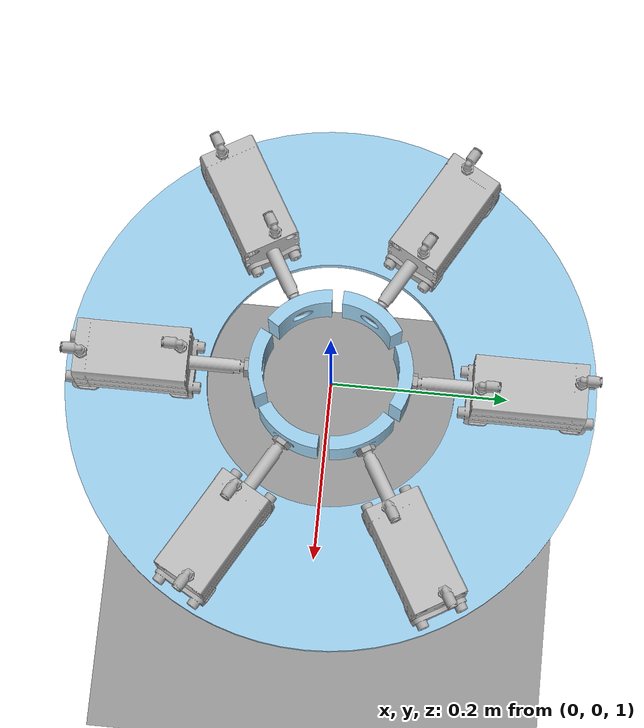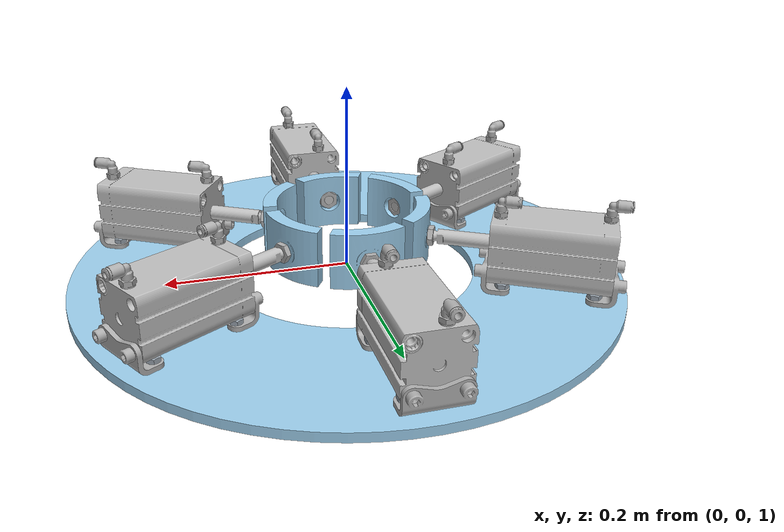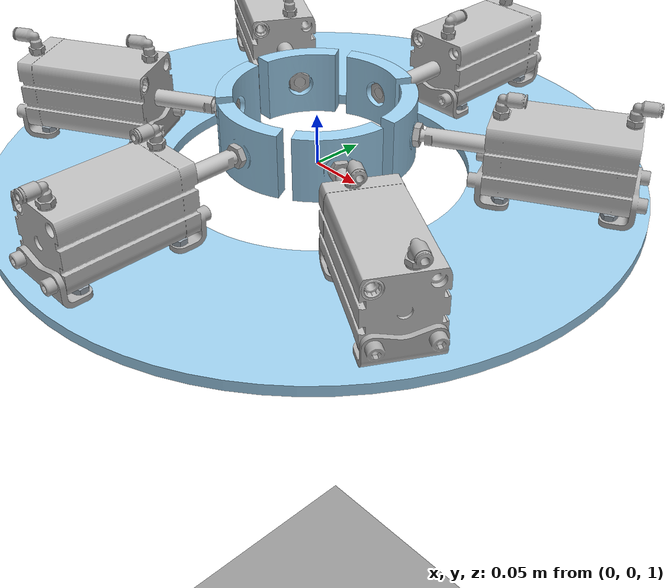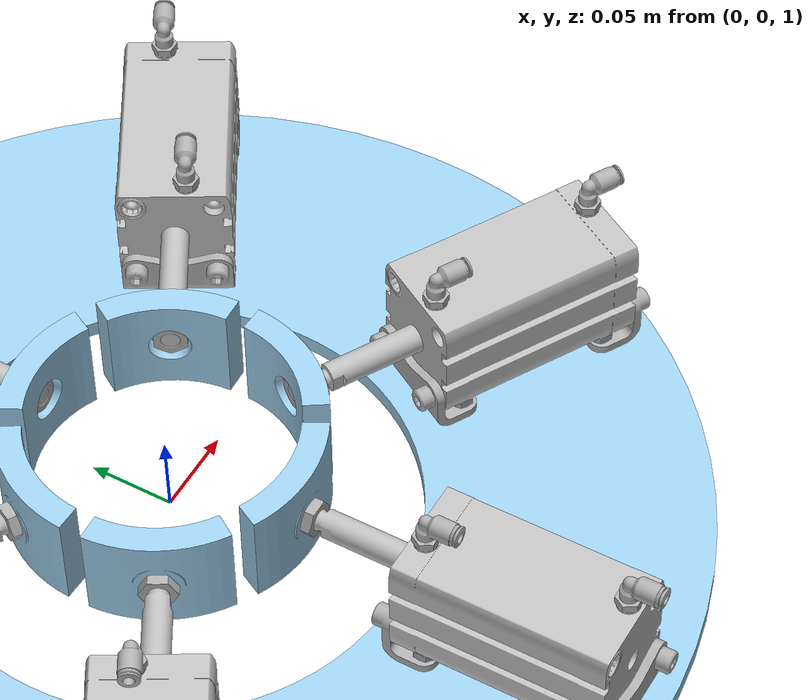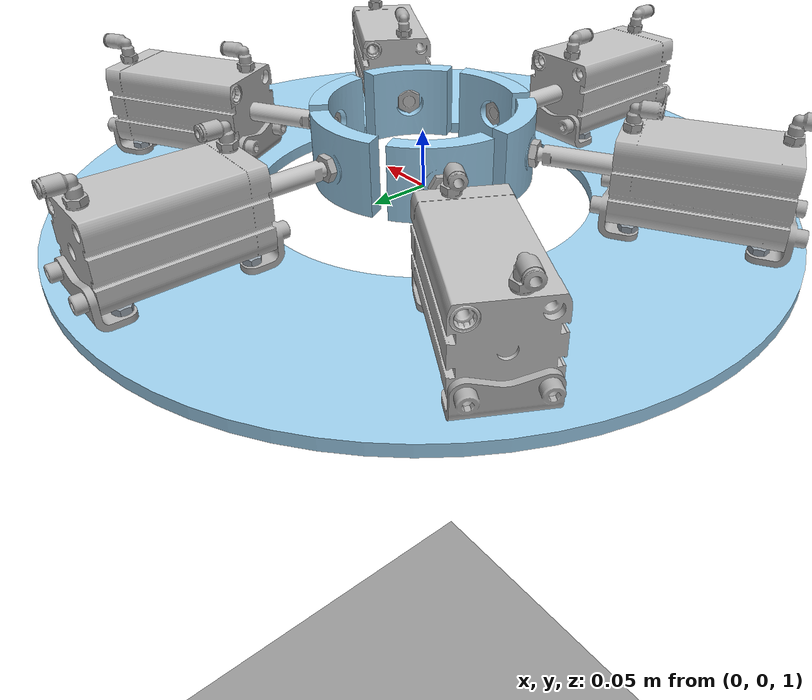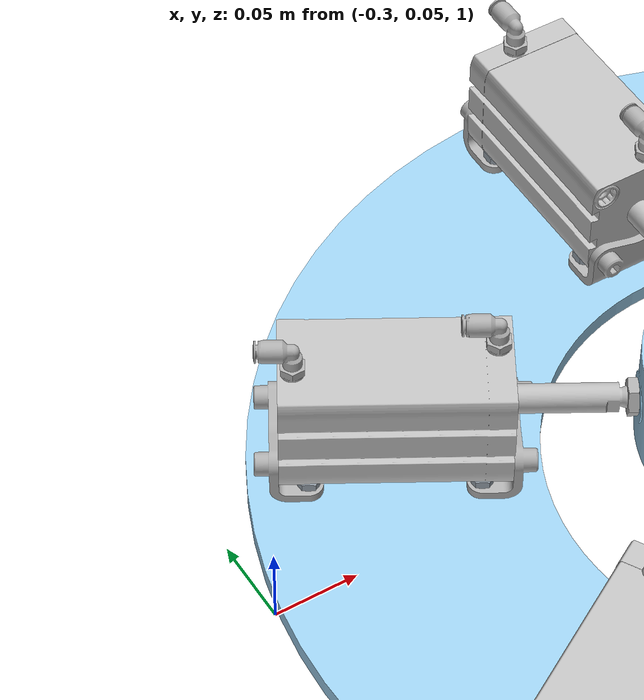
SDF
<?xml version="1.0" ?>
<sdf version="1.9">
  <world name="default">
    <!-- Include the ground plane -->
    <include>
      <uri>file://model/ground_plane.sdf</uri>
      <name>ground_plane</name>
    </include>

    <!-- Include the robot -->
    <include>
      <uri>file://model/robot.sdf</uri>
      <name>robot</name>
      <pose>0 0 1 -1.5708 0 0</pose> <!-- slightly above ground -->
    </include>

    <light name="sun" type="directional">
      <cast_shadows>true</cast_shadows>
      <pose>0 0 10 0 0 0</pose>
      <diffuse>1.0 1.0 0.9 1</diffuse>
      <specular>0.1 0.1 0.1 1</specular>
      <attenuation>
        <range>1000</range>
        <constant>0.9</constant>
        <linear>0.01</linear>
        <quadratic>0.001</quadratic>
      </attenuation>
      <direction>-0.5 0.5 -1</direction>
    </light>

    <scene>
      <ambient>0.4 0.4 0.4 1</ambient>
      <background>0.7 0.7 0.8 1</background>
      <shadows>true</shadows>
    </scene>
  </world>
</sdf>

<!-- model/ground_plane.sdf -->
<sdf version="1.9">
  <model name="ground_plane">
    <static>true</static>
    <link name="link">
      <collision name="collision">
        <geometry>
          <plane>
            <normal>0 0 1</normal>
            <size>100 100</size>
          </plane>
        </geometry>
        <surface>
          <contact>
            <collide_bitmask>0x01</collide_bitmask>
          </contact>
          <friction>
            <ode>
              <mu>1.0</mu>
              <mu2>1.0</mu2>
            </ode>
          </friction>
        </surface>
      </collision>
      <visual name="visual">
        <geometry>
          <plane>
            <normal>0 0 1</normal>
            <size>100 100</size>
          </plane>
        </geometry>
        <material>
          <script>
            <uri>file://media/materials/scripts/gazebo.material</uri>
            <name>Gazebo/Grey</name>
          </script>
        </material>
      </visual>
    </link>
  </model>
</sdf>

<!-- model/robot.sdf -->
<!-- Generated using onshape-to-robot -->
<!-- Onshape https://cad.onshape.com/documents/1ee3e8e7d3bff65cb341bad5/w/8a5c6caf79ebbf20381a9b9a/e/01657f070dd481dff05bd6b4 -->
<sdf version="1.7">
  <model name="model">
    <!-- Link base_plate -->
    <link name="base_plate">
      <inertial>
        <pose>-0.0237023 -0.0284464 -0.154045 0 0 0</pose>
        <mass>0.18158</mass>
        <inertia>
          <ixx>0.00131568</ixx>
          <ixy>0.000180204</ixy>
          <ixz>0.000186409</ixz>
          <iyy>0.00189167</iyy>
          <iyz>4.47919e-05</iyz>
          <izz>0.00107006</izz>
        </inertia>
      </inertial>
      <pose>0 0 0 0 -0 0</pose>
      <!-- Part base_plate -->
      <visual name="base_plate_visual_mesh_1">
        <pose relative_to="base_plate">7.65404e-18 0 0 -1.5708 1.5708 0</pose>
        <geometry>
          <mesh>
            <uri>model://model/assets/base_plate.stl</uri>
          </mesh>
        </geometry>
        <material>
          <ambient>0.615686 0.811765 0.929412 1</ambient>
          <diffuse>0.615686 0.811765 0.929412 1</diffuse>
          <specular>0.1 0.1 0.1 1</specular>
          <emissive>0 0 0 0</emissive>
        </material>
      </visual>
      <collision name="base_plate_collision_mesh_2">
        <pose relative_to="base_plate">7.65404e-18 0 0 -1.5708 1.5708 0</pose>
        <geometry>
          <mesh>
            <uri>model://model/assets/base_plate.stl</uri>
          </mesh>
        </geometry>
      </collision>
      <!-- Part hex_nut_grade_a___b_m8x1_25__3430b5bbd516b81b52e50f5ca3422a70 -->
      <visual name="hex_nut_grade_a___b_m8x1_25__3430b5bbd516b81b52e50f5ca3422a70_visual_mesh_1">
        <pose relative_to="base_plate">-0.24168 0.0134 -0.113553 -1.5708 -1.5708 0</pose>
        <geometry>
          <mesh>
            <uri>model://model/assets/hex_nut_grade_a___b_m8x1_25__3430b5bbd516b81b52e50f5ca3422a70.stl</uri>
          </mesh>
        </geometry>
        <material>
          <ambient>0.603922 0.647059 0.686275 1</ambient>
          <diffuse>0.603922 0.647059 0.686275 1</diffuse>
          <specular>0.1 0.1 0.1 1</specular>
          <emissive>0 0 0 0</emissive>
        </material>
      </visual>
      <collision name="hex_nut_grade_a___b_m8x1_25__3430b5bbd516b81b52e50f5ca3422a70_collision_mesh_2">
        <pose relative_to="base_plate">-0.24168 0.0134 -0.113553 -1.5708 -1.5708 0</pose>
        <geometry>
          <mesh>
            <uri>model://model/assets/hex_nut_grade_a___b_m8x1_25__3430b5bbd516b81b52e50f5ca3422a70.stl</uri>
          </mesh>
        </geometry>
      </collision>
      <!-- Part hex_nut_grade_a___b_m8x1_25__3430b5bbd516b81b52e50f5ca3422a70_2 -->
      <visual name="hex_nut_grade_a___b_m8x1_25__3430b5bbd516b81b52e50f5ca3422a70_2_visual_mesh_1">
        <pose relative_to="base_plate">-0.21918 0.0134 -0.152524 -1.5708 1.5708 0</pose>
        <geometry>
          <mesh>
            <uri>model://model/assets/hex_nut_grade_a___b_m8x1_25__3430b5bbd516b81b52e50f5ca3422a70.stl</uri>
          </mesh>
        </geometry>
        <material>
          <ambient>0.603922 0.647059 0.686275 1</ambient>
          <diffuse>0.603922 0.647059 0.686275 1</diffuse>
          <specular>0.1 0.1 0.1 1</specular>
          <emissive>0 0 0 0</emissive>
        </material>
      </visual>
      <collision name="hex_nut_grade_a___b_m8x1_25__3430b5bbd516b81b52e50f5ca3422a70_2_collision_mesh_2">
        <pose relative_to="base_plate">-0.21918 0.0134 -0.152524 -1.5708 1.5708 0</pose>
        <geometry>
          <mesh>
            <uri>model://model/assets/hex_nut_grade_a___b_m8x1_25__3430b5bbd516b81b52e50f5ca3422a70.stl</uri>
          </mesh>
        </geometry>
      </collision>
      <!-- Part hex_head_bolt_grade_a___b_m8x1_25_x_25_x_22__af70aa9de627d14e08d4f1d32024151a -->
      <visual name="hex_head_bolt_grade_a___b_m8x1_25_x_25_x_22__af70aa9de627d14e08d4f1d32024151a_visual_mesh_1">
        <pose relative_to="base_plate">-0.0225 -0.005 -0.266078 1.5708 -1.5708 0</pose>
        <geometry>
          <mesh>
            <uri>model://model/assets/hex_head_bolt_grade_a___b_m8x1_25_x_25_x_22__af70aa9de627d14e08d4f1d32024151a.stl</uri>
          </mesh>
        </geometry>
        <material>
          <ambient>0.603922 0.647059 0.686275 1</ambient>
          <diffuse>0.603922 0.647059 0.686275 1</diffuse>
          <specular>0.1 0.1 0.1 1</specular>
          <emissive>0 0 0 0</emissive>
        </material>
      </visual>
      <collision name="hex_head_bolt_grade_a___b_m8x1_25_x_25_x_22__af70aa9de627d14e08d4f1d32024151a_collision_mesh_2">
        <pose relative_to="base_plate">-0.0225 -0.005 -0.266078 1.5708 -1.5708 0</pose>
        <geometry>
          <mesh>
            <uri>model://model/assets/hex_head_bolt_grade_a___b_m8x1_25_x_25_x_22__af70aa9de627d14e08d4f1d32024151a.stl</uri>
          </mesh>
        </geometry>
      </collision>
      <!-- Part hex_nut_grade_a___b_m8x1_25__3430b5bbd516b81b52e50f5ca3422a70_3 -->
      <visual name="hex_nut_grade_a___b_m8x1_25__3430b5bbd516b81b52e50f5ca3422a70_3_visual_mesh_1">
        <pose relative_to="base_plate">-0.13864 0.0134 -0.106024 -1.5708 -1.5708 0</pose>
        <geometry>
          <mesh>
            <uri>model://model/assets/hex_nut_grade_a___b_m8x1_25__3430b5bbd516b81b52e50f5ca3422a70.stl</uri>
          </mesh>
        </geometry>
        <material>
          <ambient>0.603922 0.647059 0.686275 1</ambient>
          <diffuse>0.603922 0.647059 0.686275 1</diffuse>
          <specular>0.1 0.1 0.1 1</specular>
          <emissive>0 0 0 0</emissive>
        </material>
      </visual>
      <collision name="hex_nut_grade_a___b_m8x1_25__3430b5bbd516b81b52e50f5ca3422a70_3_collision_mesh_2">
        <pose relative_to="base_plate">-0.13864 0.0134 -0.106024 -1.5708 -1.5708 0</pose>
        <geometry>
          <mesh>
            <uri>model://model/assets/hex_nut_grade_a___b_m8x1_25__3430b5bbd516b81b52e50f5ca3422a70.stl</uri>
          </mesh>
        </geometry>
      </collision>
      <!-- Part hex_nut_grade_a___b_m8x1_25__3430b5bbd516b81b52e50f5ca3422a70_4 -->
      <visual name="hex_nut_grade_a___b_m8x1_25__3430b5bbd516b81b52e50f5ca3422a70_4_visual_mesh_1">
        <pose relative_to="base_plate">-0.16114 0.0134 -0.0670532 -1.5708 -1.5708 0</pose>
        <geometry>
          <mesh>
            <uri>model://model/assets/hex_nut_grade_a___b_m8x1_25__3430b5bbd516b81b52e50f5ca3422a70.stl</uri>
          </mesh>
        </geometry>
        <material>
          <ambient>0.603922 0.647059 0.686275 1</ambient>
          <diffuse>0.603922 0.647059 0.686275 1</diffuse>
          <specular>0.1 0.1 0.1 1</specular>
          <emissive>0 0 0 0</emissive>
        </material>
      </visual>
      <collision name="hex_nut_grade_a___b_m8x1_25__3430b5bbd516b81b52e50f5ca3422a70_4_collision_mesh_2">
        <pose relative_to="base_plate">-0.16114 0.0134 -0.0670532 -1.5708 -1.5708 0</pose>
        <geometry>
          <mesh>
            <uri>model://model/assets/hex_nut_grade_a___b_m8x1_25__3430b5bbd516b81b52e50f5ca3422a70.stl</uri>
          </mesh>
        </geometry>
      </collision>
      <!-- Part hex_head_bolt_grade_a___b_m8x1_25_x_25_x_22__af70aa9de627d14e08d4f1d32024151a_2 -->
      <visual name="hex_head_bolt_grade_a___b_m8x1_25_x_25_x_22__af70aa9de627d14e08d4f1d32024151a_2_visual_mesh_1">
        <pose relative_to="base_plate">0.0225 -0.005 -0.173078 1.5708 -1.5708 0</pose>
        <geometry>
          <mesh>
            <uri>model://model/assets/hex_head_bolt_grade_a___b_m8x1_25_x_25_x_22__af70aa9de627d14e08d4f1d32024151a.stl</uri>
          </mesh>
        </geometry>
        <material>
          <ambient>0.603922 0.647059 0.686275 1</ambient>
          <diffuse>0.603922 0.647059 0.686275 1</diffuse>
          <specular>0.1 0.1 0.1 1</specular>
          <emissive>0 0 0 0</emissive>
        </material>
      </visual>
      <collision name="hex_head_bolt_grade_a___b_m8x1_25_x_25_x_22__af70aa9de627d14e08d4f1d32024151a_2_collision_mesh_2">
        <pose relative_to="base_plate">0.0225 -0.005 -0.173078 1.5708 -1.5708 0</pose>
        <geometry>
          <mesh>
            <uri>model://model/assets/hex_head_bolt_grade_a___b_m8x1_25_x_25_x_22__af70aa9de627d14e08d4f1d32024151a.stl</uri>
          </mesh>
        </geometry>
      </collision>
      <!-- Part hex_head_bolt_grade_a___b_m8x1_25_x_25_x_22__af70aa9de627d14e08d4f1d32024151a_3 -->
      <visual name="hex_head_bolt_grade_a___b_m8x1_25_x_25_x_22__af70aa9de627d14e08d4f1d32024151a_3_visual_mesh_1">
        <pose relative_to="base_plate">0.0225 -0.005 -0.266078 1.5708 -1.5708 0</pose>
        <geometry>
          <mesh>
            <uri>model://model/assets/hex_head_bolt_grade_a___b_m8x1_25_x_25_x_22__af70aa9de627d14e08d4f1d32024151a.stl</uri>
          </mesh>
        </geometry>
        <material>
          <ambient>0.603922 0.647059 0.686275 1</ambient>
          <diffuse>0.603922 0.647059 0.686275 1</diffuse>
          <specular>0.1 0.1 0.1 1</specular>
          <emissive>0 0 0 0</emissive>
        </material>
      </visual>
      <collision name="hex_head_bolt_grade_a___b_m8x1_25_x_25_x_22__af70aa9de627d14e08d4f1d32024151a_3_collision_mesh_2">
        <pose relative_to="base_plate">0.0225 -0.005 -0.266078 1.5708 -1.5708 0</pose>
        <geometry>
          <mesh>
            <uri>model://model/assets/hex_head_bolt_grade_a___b_m8x1_25_x_25_x_22__af70aa9de627d14e08d4f1d32024151a.stl</uri>
          </mesh>
        </geometry>
      </collision>
      <!-- Part hex_head_bolt_grade_a___b_m8x1_25_x_25_x_22__af70aa9de627d14e08d4f1d32024151a_4 -->
      <visual name="hex_head_bolt_grade_a___b_m8x1_25_x_25_x_22__af70aa9de627d14e08d4f1d32024151a_4_visual_mesh_1">
        <pose relative_to="base_plate">-0.0225 -0.005 -0.173078 1.5708 -1.5708 0</pose>
        <geometry>
          <mesh>
            <uri>model://model/assets/hex_head_bolt_grade_a___b_m8x1_25_x_25_x_22__af70aa9de627d14e08d4f1d32024151a.stl</uri>
          </mesh>
        </geometry>
        <material>
          <ambient>0.603922 0.647059 0.686275 1</ambient>
          <diffuse>0.603922 0.647059 0.686275 1</diffuse>
          <specular>0.1 0.1 0.1 1</specular>
          <emissive>0 0 0 0</emissive>
        </material>
      </visual>
      <collision name="hex_head_bolt_grade_a___b_m8x1_25_x_25_x_22__af70aa9de627d14e08d4f1d32024151a_4_collision_mesh_2">
        <pose relative_to="base_plate">-0.0225 -0.005 -0.173078 1.5708 -1.5708 0</pose>
        <geometry>
          <mesh>
            <uri>model://model/assets/hex_head_bolt_grade_a___b_m8x1_25_x_25_x_22__af70aa9de627d14e08d4f1d32024151a.stl</uri>
          </mesh>
        </geometry>
      </collision>
      <!-- Part 186117_qsl_g1_8_6 -->
      <visual name="186117_qsl_g1_8_6_visual_mesh_1">
        <pose relative_to="base_plate">0.008 -0.07775 -0.273878 -3.14159 7.12763e-14 1.67618e-15</pose>
        <geometry>
          <mesh>
            <uri>model://model/assets/186117_qsl_g1_8_6.stl</uri>
          </mesh>
        </geometry>
        <material>
          <ambient>0.690196 0.690196 0.690196 1</ambient>
          <diffuse>0.690196 0.690196 0.690196 1</diffuse>
          <specular>0.1 0.1 0.1 1</specular>
          <emissive>0 0 0 0</emissive>
        </material>
      </visual>
      <collision name="186117_qsl_g1_8_6_collision_mesh_2">
        <pose relative_to="base_plate">0.008 -0.07775 -0.273878 -3.14159 7.12763e-14 1.67618e-15</pose>
        <geometry>
          <mesh>
            <uri>model://model/assets/186117_qsl_g1_8_6.stl</uri>
          </mesh>
        </geometry>
      </collision>
      <!-- Part 186117_qsl_g1_8_6_2 -->
      <visual name="186117_qsl_g1_8_6_2_visual_mesh_1">
        <pose relative_to="base_plate">-0.008 -0.07775 -0.165278 -3.14159 7.12763e-14 1.67618e-15</pose>
        <geometry>
          <mesh>
            <uri>model://model/assets/186117_qsl_g1_8_6.stl</uri>
          </mesh>
        </geometry>
        <material>
          <ambient>0.690196 0.690196 0.690196 1</ambient>
          <diffuse>0.690196 0.690196 0.690196 1</diffuse>
          <specular>0.1 0.1 0.1 1</specular>
          <emissive>0 0 0 0</emissive>
        </material>
      </visual>
      <collision name="186117_qsl_g1_8_6_2_collision_mesh_2">
        <pose relative_to="base_plate">-0.008 -0.07775 -0.165278 -3.14159 7.12763e-14 1.67618e-15</pose>
        <geometry>
          <mesh>
            <uri>model://model/assets/186117_qsl_g1_8_6.stl</uri>
          </mesh>
        </geometry>
      </collision>
      <!-- Part din_439_b___m12x1_25_f -->
      <visual name="din_439_b___m12x1_25_f_visual_mesh_1">
        <pose relative_to="base_plate">1.03794e-14 -0.045 -0.0783172 1.5708 7.1422e-14 -1.28107e-56</pose>
        <geometry>
          <mesh>
            <uri>model://model/assets/din_439_b___m12x1_25_f.stl</uri>
          </mesh>
        </geometry>
        <material>
          <ambient>0.690196 0.690196 0.690196 1</ambient>
          <diffuse>0.690196 0.690196 0.690196 1</diffuse>
          <specular>0.1 0.1 0.1 1</specular>
          <emissive>0 0 0 0</emissive>
        </material>
      </visual>
      <collision name="din_439_b___m12x1_25_f_collision_mesh_2">
        <pose relative_to="base_plate">1.03794e-14 -0.045 -0.0783172 1.5708 7.1422e-14 -1.28107e-56</pose>
        <geometry>
          <mesh>
            <uri>model://model/assets/din_439_b___m12x1_25_f.stl</uri>
          </mesh>
        </geometry>
      </collision>
      <!-- Part gripper_cup -->
      <visual name="gripper_cup_visual_mesh_1">
        <pose relative_to="base_plate">1.54889e-14 -0.015 -0.00531717 1.5708 -0.479966 3.70765e-29</pose>
        <geometry>
          <mesh>
            <uri>model://model/assets/gripper_cup.stl</uri>
          </mesh>
        </geometry>
        <material>
          <ambient>0.615686 0.811765 0.929412 1</ambient>
          <diffuse>0.615686 0.811765 0.929412 1</diffuse>
          <specular>0.1 0.1 0.1 1</specular>
          <emissive>0 0 0 0</emissive>
        </material>
      </visual>
      <collision name="gripper_cup_collision_mesh_2">
        <pose relative_to="base_plate">1.54889e-14 -0.015 -0.00531717 1.5708 -0.479966 3.70765e-29</pose>
        <geometry>
          <mesh>
            <uri>model://model/assets/gripper_cup.stl</uri>
          </mesh>
        </geometry>
      </collision>
      <!-- Part 537243_hna_50____1 -->
      <visual name="537243_hna_50____1_visual_mesh_1">
        <pose relative_to="base_plate">6.93889e-18 -1.27513e-42 -0.287078 -3.14159 -1.5708 0</pose>
        <geometry>
          <mesh>
            <uri>model://model/assets/537243_hna_50____1.stl</uri>
          </mesh>
        </geometry>
        <material>
          <ambient>0.690196 0.690196 0.690196 1</ambient>
          <diffuse>0.690196 0.690196 0.690196 1</diffuse>
          <specular>0.1 0.1 0.1 1</specular>
          <emissive>0 0 0 0</emissive>
        </material>
      </visual>
      <collision name="537243_hna_50____1_collision_mesh_2">
        <pose relative_to="base_plate">6.93889e-18 -1.27513e-42 -0.287078 -3.14159 -1.5708 0</pose>
        <geometry>
          <mesh>
            <uri>model://model/assets/537243_hna_50____1.stl</uri>
          </mesh>
        </geometry>
      </collision>
      <!-- Part 537243_hna_50____1_2 -->
      <visual name="537243_hna_50____1_2_visual_mesh_1">
        <pose relative_to="base_plate">4.39232e-15 2.26861e-31 -0.152078 -3.14159 1.5708 0</pose>
        <geometry>
          <mesh>
            <uri>model://model/assets/537243_hna_50____1.stl</uri>
          </mesh>
        </geometry>
        <material>
          <ambient>0.690196 0.690196 0.690196 1</ambient>
          <diffuse>0.690196 0.690196 0.690196 1</diffuse>
          <specular>0.1 0.1 0.1 1</specular>
          <emissive>0 0 0 0</emissive>
        </material>
      </visual>
      <collision name="537243_hna_50____1_2_collision_mesh_2">
        <pose relative_to="base_plate">4.39232e-15 2.26861e-31 -0.152078 -3.14159 1.5708 0</pose>
        <geometry>
          <mesh>
            <uri>model://model/assets/537243_hna_50____1.stl</uri>
          </mesh>
        </geometry>
      </collision>
      <!-- Part din_439_b___m12x1_25_f_2 -->
      <visual name="din_439_b___m12x1_25_f_2_visual_mesh_1">
        <pose relative_to="base_plate">9.53994e-15 -0.045 -0.0903172 1.5708 -2.02737e-28 -1.5708</pose>
        <geometry>
          <mesh>
            <uri>model://model/assets/din_439_b___m12x1_25_f.stl</uri>
          </mesh>
        </geometry>
        <material>
          <ambient>0.690196 0.690196 0.690196 1</ambient>
          <diffuse>0.690196 0.690196 0.690196 1</diffuse>
          <specular>0.1 0.1 0.1 1</specular>
          <emissive>0 0 0 0</emissive>
        </material>
      </visual>
      <collision name="din_439_b___m12x1_25_f_2_collision_mesh_2">
        <pose relative_to="base_plate">9.53994e-15 -0.045 -0.0903172 1.5708 -2.02737e-28 -1.5708</pose>
        <geometry>
          <mesh>
            <uri>model://model/assets/din_439_b___m12x1_25_f.stl</uri>
          </mesh>
        </geometry>
      </collision>
      <!-- Part 536309_adn_80_p____z -->
      <visual name="536309_adn_80_p____z_visual_mesh_1">
        <pose relative_to="base_plate">4.20744e-15 -0.045 -0.157078 -7.12763e-14 -5.87621e-16 -1.5708</pose>
        <geometry>
          <mesh>
            <uri>model://model/assets/536309_adn_80_p____z.stl</uri>
          </mesh>
        </geometry>
        <material>
          <ambient>0.74902 0.74902 0.74902 1</ambient>
          <diffuse>0.74902 0.74902 0.74902 1</diffuse>
          <specular>0.1 0.1 0.1 1</specular>
          <emissive>0 0 0 0</emissive>
        </material>
      </visual>
      <collision name="536309_adn_80_p____z_collision_mesh_2">
        <pose relative_to="base_plate">4.20744e-15 -0.045 -0.157078 -7.12763e-14 -5.87621e-16 -1.5708</pose>
        <geometry>
          <mesh>
            <uri>model://model/assets/536309_adn_80_p____z.stl</uri>
          </mesh>
        </geometry>
      </collision>
      <!-- Part 536309_adn_80_p_a__ks -->
      <visual name="536309_adn_80_p_a__ks_visual_mesh_1">
        <pose relative_to="base_plate">8.25544e-15 -0.045 -0.108297 -1.5708 1.5708 0</pose>
        <geometry>
          <mesh>
            <uri>model://model/assets/536309_adn_80_p_a__ks.stl</uri>
          </mesh>
        </geometry>
        <material>
          <ambient>0.74902 0.74902 0.74902 1</ambient>
          <diffuse>0.74902 0.74902 0.74902 1</diffuse>
          <specular>0.1 0.1 0.1 1</specular>
          <emissive>0 0 0 0</emissive>
        </material>
      </visual>
      <collision name="536309_adn_80_p_a__ks_collision_mesh_2">
        <pose relative_to="base_plate">8.25544e-15 -0.045 -0.108297 -1.5708 1.5708 0</pose>
        <geometry>
          <mesh>
            <uri>model://model/assets/536309_adn_80_p_a__ks.stl</uri>
          </mesh>
        </geometry>
      </collision>
    </link>
    <!-- Link 537243_hna_50____125 -->
    <link name="537243_hna_50____125">
      <inertial>
        <pose>0 0 0 0 0 0</pose>
        <mass>1e-09</mass>
        <inertia>
          <ixx>1e-09</ixx>
          <ixy>0</ixy>
          <ixz>0</ixz>
          <iyy>1e-09</iyy>
          <iyz>0</iyz>
          <izz>1e-09</izz>
        </inertia>
      </inertial>
      <pose>0 0 0 0 -0 0</pose>
      <!-- Part 537243_hna_50____1_3 -->
      <visual name="537243_hna_50____1_3_visual_mesh_1">
        <pose relative_to="537243_hna_50____125">0.248616 -1.24938e-42 -0.143539 -3.57072e-41 -0.523599 -3.14159</pose>
        <geometry>
          <mesh>
            <uri>model://model/assets/537243_hna_50____1.stl</uri>
          </mesh>
        </geometry>
        <material>
          <ambient>0.690196 0.690196 0.690196 1</ambient>
          <diffuse>0.690196 0.690196 0.690196 1</diffuse>
          <specular>0.1 0.1 0.1 1</specular>
          <emissive>0 0 0 0</emissive>
        </material>
      </visual>
      <collision name="537243_hna_50____1_3_collision_mesh_2">
        <pose relative_to="537243_hna_50____125">0.248616 -1.24938e-42 -0.143539 -3.57072e-41 -0.523599 -3.14159</pose>
        <geometry>
          <mesh>
            <uri>model://model/assets/537243_hna_50____1.stl</uri>
          </mesh>
        </geometry>
      </collision>
      <!-- Part 537243_hna_50____1_4 -->
      <visual name="537243_hna_50____1_4_visual_mesh_1">
        <pose relative_to="537243_hna_50____125">0.131703 2.26861e-31 -0.0760388 -3.14159 0.523599 -4.35676e-29</pose>
        <geometry>
          <mesh>
            <uri>model://model/assets/537243_hna_50____1.stl</uri>
          </mesh>
        </geometry>
        <material>
          <ambient>0.690196 0.690196 0.690196 1</ambient>
          <diffuse>0.690196 0.690196 0.690196 1</diffuse>
          <specular>0.1 0.1 0.1 1</specular>
          <emissive>0 0 0 0</emissive>
        </material>
      </visual>
      <collision name="537243_hna_50____1_4_collision_mesh_2">
        <pose relative_to="537243_hna_50____125">0.131703 2.26861e-31 -0.0760388 -3.14159 0.523599 -4.35676e-29</pose>
        <geometry>
          <mesh>
            <uri>model://model/assets/537243_hna_50____1.stl</uri>
          </mesh>
        </geometry>
      </collision>
    </link>
    <!-- Link 537243_hna_50____125_2 -->
    <link name="537243_hna_50____125_2">
      <inertial>
        <pose>0 0 0 0 0 0</pose>
        <mass>1e-09</mass>
        <inertia>
          <ixx>1e-09</ixx>
          <ixy>0</ixy>
          <ixz>0</ixz>
          <iyy>1e-09</iyy>
          <iyz>0</iyz>
          <izz>1e-09</izz>
        </inertia>
      </inertial>
      <pose>0 0 0 0 -0 0</pose>
      <!-- Part 537243_hna_50____1_5 -->
      <visual name="537243_hna_50____1_5_visual_mesh_1">
        <pose relative_to="537243_hna_50____125_2">0.248616 -1.19789e-42 0.143539 -4.65657e-41 0.523599 -3.14159</pose>
        <geometry>
          <mesh>
            <uri>model://model/assets/537243_hna_50____1.stl</uri>
          </mesh>
        </geometry>
        <material>
          <ambient>0.690196 0.690196 0.690196 1</ambient>
          <diffuse>0.690196 0.690196 0.690196 1</diffuse>
          <specular>0.1 0.1 0.1 1</specular>
          <emissive>0 0 0 0</emissive>
        </material>
      </visual>
      <collision name="537243_hna_50____1_5_collision_mesh_2">
        <pose relative_to="537243_hna_50____125_2">0.248616 -1.19789e-42 0.143539 -4.65657e-41 0.523599 -3.14159</pose>
        <geometry>
          <mesh>
            <uri>model://model/assets/537243_hna_50____1.stl</uri>
          </mesh>
        </geometry>
      </collision>
      <!-- Part 537243_hna_50____1_6 -->
      <visual name="537243_hna_50____1_6_visual_mesh_1">
        <pose relative_to="537243_hna_50____125_2">0.131703 2.26861e-31 0.0760388 -3.14159 -0.523599 -4.35676e-29</pose>
        <geometry>
          <mesh>
            <uri>model://model/assets/537243_hna_50____1.stl</uri>
          </mesh>
        </geometry>
        <material>
          <ambient>0.690196 0.690196 0.690196 1</ambient>
          <diffuse>0.690196 0.690196 0.690196 1</diffuse>
          <specular>0.1 0.1 0.1 1</specular>
          <emissive>0 0 0 0</emissive>
        </material>
      </visual>
      <collision name="537243_hna_50____1_6_collision_mesh_2">
        <pose relative_to="537243_hna_50____125_2">0.131703 2.26861e-31 0.0760388 -3.14159 -0.523599 -4.35676e-29</pose>
        <geometry>
          <mesh>
            <uri>model://model/assets/537243_hna_50____1.stl</uri>
          </mesh>
        </geometry>
      </collision>
    </link>
    <!-- Link 537243_hna_50____125_3 -->
    <link name="537243_hna_50____125_3">
      <inertial>
        <pose>0 0 0 0 0 0</pose>
        <mass>1e-09</mass>
        <inertia>
          <ixx>1e-09</ixx>
          <ixy>0</ixy>
          <ixz>0</ixz>
          <iyy>1e-09</iyy>
          <iyz>0</iyz>
          <izz>1e-09</izz>
        </inertia>
      </inertial>
      <pose>0 0 0 0 -0 0</pose>
      <!-- Part 537243_hna_50____1_7 -->
      <visual name="537243_hna_50____1_7_visual_mesh_1">
        <pose relative_to="537243_hna_50____125_3">2.6381e-17 -1.17214e-42 0.287078 -3.14159 1.5708 0</pose>
        <geometry>
          <mesh>
            <uri>model://model/assets/537243_hna_50____1.stl</uri>
          </mesh>
        </geometry>
        <material>
          <ambient>0.690196 0.690196 0.690196 1</ambient>
          <diffuse>0.690196 0.690196 0.690196 1</diffuse>
          <specular>0.1 0.1 0.1 1</specular>
          <emissive>0 0 0 0</emissive>
        </material>
      </visual>
      <collision name="537243_hna_50____1_7_collision_mesh_2">
        <pose relative_to="537243_hna_50____125_3">2.6381e-17 -1.17214e-42 0.287078 -3.14159 1.5708 0</pose>
        <geometry>
          <mesh>
            <uri>model://model/assets/537243_hna_50____1.stl</uri>
          </mesh>
        </geometry>
      </collision>
      <!-- Part 537243_hna_50____1_8 -->
      <visual name="537243_hna_50____1_8_visual_mesh_1">
        <pose relative_to="537243_hna_50____125_3">-4.37553e-15 2.26861e-31 0.152078 -3.14159 -1.5708 0</pose>
        <geometry>
          <mesh>
            <uri>model://model/assets/537243_hna_50____1.stl</uri>
          </mesh>
        </geometry>
        <material>
          <ambient>0.690196 0.690196 0.690196 1</ambient>
          <diffuse>0.690196 0.690196 0.690196 1</diffuse>
          <specular>0.1 0.1 0.1 1</specular>
          <emissive>0 0 0 0</emissive>
        </material>
      </visual>
      <collision name="537243_hna_50____1_8_collision_mesh_2">
        <pose relative_to="537243_hna_50____125_3">-4.37553e-15 2.26861e-31 0.152078 -3.14159 -1.5708 0</pose>
        <geometry>
          <mesh>
            <uri>model://model/assets/537243_hna_50____1.stl</uri>
          </mesh>
        </geometry>
      </collision>
    </link>
    <!-- Link piston_cup_assembly -->
    <link name="piston_cup_assembly">
      <inertial>
        <pose>0.0693571 -0.045 -0.0400436 0 0 0</pose>
        <mass>0.0684937</mass>
        <inertia>
          <ixx>4.68003e-05</ixx>
          <ixy>-1.05062e-11</ixy>
          <ixz>-1.33609e-05</ixz>
          <iyy>3.43116e-05</iyy>
          <iyz>-1.90835e-11</iyz>
          <izz>3.13723e-05</izz>
        </inertia>
      </inertial>
      <pose>0 0 0 0 -0 0</pose>
      <!-- Part din_439_b___m12x1_25_f_3 -->
      <visual name="din_439_b___m12x1_25_f_3_visual_mesh_1">
        <pose relative_to="piston_cup_assembly">0.0678247 -0.045 -0.0391586 1.5708 -1.0472 3.10671e-43</pose>
        <geometry>
          <mesh>
            <uri>model://model/assets/din_439_b___m12x1_25_f.stl</uri>
          </mesh>
        </geometry>
        <material>
          <ambient>0.690196 0.690196 0.690196 1</ambient>
          <diffuse>0.690196 0.690196 0.690196 1</diffuse>
          <specular>0.1 0.1 0.1 1</specular>
          <emissive>0 0 0 0</emissive>
        </material>
      </visual>
      <collision name="din_439_b___m12x1_25_f_3_collision_mesh_2">
        <pose relative_to="piston_cup_assembly">0.0678247 -0.045 -0.0391586 1.5708 -1.0472 3.10671e-43</pose>
        <geometry>
          <mesh>
            <uri>model://model/assets/din_439_b___m12x1_25_f.stl</uri>
          </mesh>
        </geometry>
      </collision>
      <!-- Part gripper_cup_2 -->
      <visual name="gripper_cup_2_visual_mesh_1">
        <pose relative_to="piston_cup_assembly">0.0046048 -0.015 -0.00265858 1.5708 -1.52716 6.3855e-43</pose>
        <geometry>
          <mesh>
            <uri>model://model/assets/gripper_cup.stl</uri>
          </mesh>
        </geometry>
        <material>
          <ambient>0.615686 0.811765 0.929412 1</ambient>
          <diffuse>0.615686 0.811765 0.929412 1</diffuse>
          <specular>0.1 0.1 0.1 1</specular>
          <emissive>0 0 0 0</emissive>
        </material>
      </visual>
      <collision name="gripper_cup_2_collision_mesh_2">
        <pose relative_to="piston_cup_assembly">0.0046048 -0.015 -0.00265858 1.5708 -1.52716 6.3855e-43</pose>
        <geometry>
          <mesh>
            <uri>model://model/assets/gripper_cup.stl</uri>
          </mesh>
        </geometry>
      </collision>
      <!-- Part din_439_b___m12x1_25_f_4 -->
      <visual name="din_439_b___m12x1_25_f_4_visual_mesh_1">
        <pose relative_to="piston_cup_assembly">0.078217 -0.045 -0.0451586 2.61799 -1.02057e-28 -1.5708</pose>
        <geometry>
          <mesh>
            <uri>model://model/assets/din_439_b___m12x1_25_f.stl</uri>
          </mesh>
        </geometry>
        <material>
          <ambient>0.690196 0.690196 0.690196 1</ambient>
          <diffuse>0.690196 0.690196 0.690196 1</diffuse>
          <specular>0.1 0.1 0.1 1</specular>
          <emissive>0 0 0 0</emissive>
        </material>
      </visual>
      <collision name="din_439_b___m12x1_25_f_4_collision_mesh_2">
        <pose relative_to="piston_cup_assembly">0.078217 -0.045 -0.0451586 2.61799 -1.02057e-28 -1.5708</pose>
        <geometry>
          <mesh>
            <uri>model://model/assets/din_439_b___m12x1_25_f.stl</uri>
          </mesh>
        </geometry>
      </collision>
      <!-- Part 536309_adn_80_p____z_2 -->
      <visual name="536309_adn_80_p____z_2_visual_mesh_1">
        <pose relative_to="piston_cup_assembly">0.136033 -0.045 -0.0785388 1.0472 -2.93811e-16 -1.5708</pose>
        <geometry>
          <mesh>
            <uri>model://model/assets/536309_adn_80_p____z.stl</uri>
          </mesh>
        </geometry>
        <material>
          <ambient>0.74902 0.74902 0.74902 1</ambient>
          <diffuse>0.74902 0.74902 0.74902 1</diffuse>
          <specular>0.1 0.1 0.1 1</specular>
          <emissive>0 0 0 0</emissive>
        </material>
      </visual>
      <collision name="536309_adn_80_p____z_2_collision_mesh_2">
        <pose relative_to="piston_cup_assembly">0.136033 -0.045 -0.0785388 1.0472 -2.93811e-16 -1.5708</pose>
        <geometry>
          <mesh>
            <uri>model://model/assets/536309_adn_80_p____z.stl</uri>
          </mesh>
        </geometry>
      </collision>
      <!-- Part 536309_adn_80_p_a__ks_2 -->
      <visual name="536309_adn_80_p_a__ks_2_visual_mesh_1">
        <pose relative_to="piston_cup_assembly">0.0937875 -0.045 -0.0541483 -1.5708 0.523599 -5.48992e-18</pose>
        <geometry>
          <mesh>
            <uri>model://model/assets/536309_adn_80_p_a__ks.stl</uri>
          </mesh>
        </geometry>
        <material>
          <ambient>0.74902 0.74902 0.74902 1</ambient>
          <diffuse>0.74902 0.74902 0.74902 1</diffuse>
          <specular>0.1 0.1 0.1 1</specular>
          <emissive>0 0 0 0</emissive>
        </material>
      </visual>
      <collision name="536309_adn_80_p_a__ks_2_collision_mesh_2">
        <pose relative_to="piston_cup_assembly">0.0937875 -0.045 -0.0541483 -1.5708 0.523599 -5.48992e-18</pose>
        <geometry>
          <mesh>
            <uri>model://model/assets/536309_adn_80_p_a__ks.stl</uri>
          </mesh>
        </geometry>
      </collision>
    </link>
    <!-- Link piston_cup_assembly_2 -->
    <link name="piston_cup_assembly_2">
      <inertial>
        <pose>0.0693573 -0.045 0.0400432 0 0 0</pose>
        <mass>0.0684937</mass>
        <inertia>
          <ixx>4.68002e-05</ixx>
          <ixy>1.12737e-11</ixy>
          <ixz>1.3361e-05</ixz>
          <iyy>3.43116e-05</iyy>
          <iyz>-1.86404e-11</iyz>
          <izz>3.13725e-05</izz>
        </inertia>
      </inertial>
      <pose>0 0 0 0 -0 0</pose>
      <!-- Part din_439_b___m12x1_25_f_5 -->
      <visual name="din_439_b___m12x1_25_f_5_visual_mesh_1">
        <pose relative_to="piston_cup_assembly_2">0.0678247 -0.045 0.0391586 -1.5708 -1.0472 3.14159</pose>
        <geometry>
          <mesh>
            <uri>model://model/assets/din_439_b___m12x1_25_f.stl</uri>
          </mesh>
        </geometry>
        <material>
          <ambient>0.690196 0.690196 0.690196 1</ambient>
          <diffuse>0.690196 0.690196 0.690196 1</diffuse>
          <specular>0.1 0.1 0.1 1</specular>
          <emissive>0 0 0 0</emissive>
        </material>
      </visual>
      <collision name="din_439_b___m12x1_25_f_5_collision_mesh_2">
        <pose relative_to="piston_cup_assembly_2">0.0678247 -0.045 0.0391586 -1.5708 -1.0472 3.14159</pose>
        <geometry>
          <mesh>
            <uri>model://model/assets/din_439_b___m12x1_25_f.stl</uri>
          </mesh>
        </geometry>
      </collision>
      <!-- Part gripper_cup_3 -->
      <visual name="gripper_cup_3_visual_mesh_1">
        <pose relative_to="piston_cup_assembly_2">0.0046048 -0.015 0.00265858 -1.5708 -0.567232 3.14159</pose>
        <geometry>
          <mesh>
            <uri>model://model/assets/gripper_cup.stl</uri>
          </mesh>
        </geometry>
        <material>
          <ambient>0.615686 0.811765 0.929412 1</ambient>
          <diffuse>0.615686 0.811765 0.929412 1</diffuse>
          <specular>0.1 0.1 0.1 1</specular>
          <emissive>0 0 0 0</emissive>
        </material>
      </visual>
      <collision name="gripper_cup_3_collision_mesh_2">
        <pose relative_to="piston_cup_assembly_2">0.0046048 -0.015 0.00265858 -1.5708 -0.567232 3.14159</pose>
        <geometry>
          <mesh>
            <uri>model://model/assets/gripper_cup.stl</uri>
          </mesh>
        </geometry>
      </collision>
      <!-- Part din_439_b___m12x1_25_f_6 -->
      <visual name="din_439_b___m12x1_25_f_6_visual_mesh_1">
        <pose relative_to="piston_cup_assembly_2">0.078217 -0.045 0.0451586 -2.61799 1.0068e-28 -1.5708</pose>
        <geometry>
          <mesh>
            <uri>model://model/assets/din_439_b___m12x1_25_f.stl</uri>
          </mesh>
        </geometry>
        <material>
          <ambient>0.690196 0.690196 0.690196 1</ambient>
          <diffuse>0.690196 0.690196 0.690196 1</diffuse>
          <specular>0.1 0.1 0.1 1</specular>
          <emissive>0 0 0 0</emissive>
        </material>
      </visual>
      <collision name="din_439_b___m12x1_25_f_6_collision_mesh_2">
        <pose relative_to="piston_cup_assembly_2">0.078217 -0.045 0.0451586 -2.61799 1.0068e-28 -1.5708</pose>
        <geometry>
          <mesh>
            <uri>model://model/assets/din_439_b___m12x1_25_f.stl</uri>
          </mesh>
        </geometry>
      </collision>
      <!-- Part 536309_adn_80_p____z_3 -->
      <visual name="536309_adn_80_p____z_3_visual_mesh_1">
        <pose relative_to="piston_cup_assembly_2">0.136033 -0.045 0.0785388 2.0944 2.93811e-16 -1.5708</pose>
        <geometry>
          <mesh>
            <uri>model://model/assets/536309_adn_80_p____z.stl</uri>
          </mesh>
        </geometry>
        <material>
          <ambient>0.74902 0.74902 0.74902 1</ambient>
          <diffuse>0.74902 0.74902 0.74902 1</diffuse>
          <specular>0.1 0.1 0.1 1</specular>
          <emissive>0 0 0 0</emissive>
        </material>
      </visual>
      <collision name="536309_adn_80_p____z_3_collision_mesh_2">
        <pose relative_to="piston_cup_assembly_2">0.136033 -0.045 0.0785388 2.0944 2.93811e-16 -1.5708</pose>
        <geometry>
          <mesh>
            <uri>model://model/assets/536309_adn_80_p____z.stl</uri>
          </mesh>
        </geometry>
      </collision>
      <!-- Part 536309_adn_80_p_a__ks_3 -->
      <visual name="536309_adn_80_p_a__ks_3_visual_mesh_1">
        <pose relative_to="piston_cup_assembly_2">0.0937875 -0.045 0.0541483 -1.5708 -0.523599 -3.75393e-17</pose>
        <geometry>
          <mesh>
            <uri>model://model/assets/536309_adn_80_p_a__ks.stl</uri>
          </mesh>
        </geometry>
        <material>
          <ambient>0.74902 0.74902 0.74902 1</ambient>
          <diffuse>0.74902 0.74902 0.74902 1</diffuse>
          <specular>0.1 0.1 0.1 1</specular>
          <emissive>0 0 0 0</emissive>
        </material>
      </visual>
      <collision name="536309_adn_80_p_a__ks_3_collision_mesh_2">
        <pose relative_to="piston_cup_assembly_2">0.0937875 -0.045 0.0541483 -1.5708 -0.523599 -3.75393e-17</pose>
        <geometry>
          <mesh>
            <uri>model://model/assets/536309_adn_80_p_a__ks.stl</uri>
          </mesh>
        </geometry>
      </collision>
    </link>
    <!-- Link piston_cup_assembly_3 -->
    <link name="piston_cup_assembly_3">
      <inertial>
        <pose>2.31584e-07 -0.045 0.0800868 0 0 0</pose>
        <mass>0.0684937</mass>
        <inertia>
          <ixx>2.36585e-05</ixx>
          <ixy>2.17799e-11</ixy>
          <ixz>-9.82143e-11</ixz>
          <iyy>3.43116e-05</iyy>
          <iyz>4.43108e-13</iyz>
          <izz>5.45142e-05</izz>
        </inertia>
      </inertial>
      <pose>0 0 0 0 -0 0</pose>
      <!-- Part din_439_b___m12x1_25_f_7 -->
      <visual name="din_439_b___m12x1_25_f_7_visual_mesh_1">
        <pose relative_to="piston_cup_assembly_3">-1.03698e-14 -0.045 0.0783172 -1.5708 -7.14977e-14 3.14159</pose>
        <geometry>
          <mesh>
            <uri>model://model/assets/din_439_b___m12x1_25_f.stl</uri>
          </mesh>
        </geometry>
        <material>
          <ambient>0.690196 0.690196 0.690196 1</ambient>
          <diffuse>0.690196 0.690196 0.690196 1</diffuse>
          <specular>0.1 0.1 0.1 1</specular>
          <emissive>0 0 0 0</emissive>
        </material>
      </visual>
      <collision name="din_439_b___m12x1_25_f_7_collision_mesh_2">
        <pose relative_to="piston_cup_assembly_3">-1.03698e-14 -0.045 0.0783172 -1.5708 -7.14977e-14 3.14159</pose>
        <geometry>
          <mesh>
            <uri>model://model/assets/din_439_b___m12x1_25_f.stl</uri>
          </mesh>
        </geometry>
      </collision>
      <!-- Part gripper_cup_4 -->
      <visual name="gripper_cup_4_visual_mesh_1">
        <pose relative_to="piston_cup_assembly_3">-1.54883e-14 -0.015 0.00531717 -1.5708 0.479966 3.14159</pose>
        <geometry>
          <mesh>
            <uri>model://model/assets/gripper_cup.stl</uri>
          </mesh>
        </geometry>
        <material>
          <ambient>0.615686 0.811765 0.929412 1</ambient>
          <diffuse>0.615686 0.811765 0.929412 1</diffuse>
          <specular>0.1 0.1 0.1 1</specular>
          <emissive>0 0 0 0</emissive>
        </material>
      </visual>
      <collision name="gripper_cup_4_collision_mesh_2">
        <pose relative_to="piston_cup_assembly_3">-1.54883e-14 -0.015 0.00531717 -1.5708 0.479966 3.14159</pose>
        <geometry>
          <mesh>
            <uri>model://model/assets/gripper_cup.stl</uri>
          </mesh>
        </geometry>
      </collision>
      <!-- Part din_439_b___m12x1_25_f_8 -->
      <visual name="din_439_b___m12x1_25_f_8_visual_mesh_1">
        <pose relative_to="piston_cup_assembly_3">-9.52888e-15 -0.045 0.0903172 -1.5708 4.25748e-27 -1.5708</pose>
        <geometry>
          <mesh>
            <uri>model://model/assets/din_439_b___m12x1_25_f.stl</uri>
          </mesh>
        </geometry>
        <material>
          <ambient>0.690196 0.690196 0.690196 1</ambient>
          <diffuse>0.690196 0.690196 0.690196 1</diffuse>
          <specular>0.1 0.1 0.1 1</specular>
          <emissive>0 0 0 0</emissive>
        </material>
      </visual>
      <collision name="din_439_b___m12x1_25_f_8_collision_mesh_2">
        <pose relative_to="piston_cup_assembly_3">-9.52888e-15 -0.045 0.0903172 -1.5708 4.25748e-27 -1.5708</pose>
        <geometry>
          <mesh>
            <uri>model://model/assets/din_439_b___m12x1_25_f.stl</uri>
          </mesh>
        </geometry>
      </collision>
      <!-- Part 536309_adn_80_p____z_4 -->
      <visual name="536309_adn_80_p____z_4_visual_mesh_1">
        <pose relative_to="piston_cup_assembly_3">-4.19004e-15 -0.045 0.157078 3.14159 5.87621e-16 -1.5708</pose>
        <geometry>
          <mesh>
            <uri>model://model/assets/536309_adn_80_p____z.stl</uri>
          </mesh>
        </geometry>
        <material>
          <ambient>0.74902 0.74902 0.74902 1</ambient>
          <diffuse>0.74902 0.74902 0.74902 1</diffuse>
          <specular>0.1 0.1 0.1 1</specular>
          <emissive>0 0 0 0</emissive>
        </material>
      </visual>
      <collision name="536309_adn_80_p____z_4_collision_mesh_2">
        <pose relative_to="piston_cup_assembly_3">-4.19004e-15 -0.045 0.157078 3.14159 5.87621e-16 -1.5708</pose>
        <geometry>
          <mesh>
            <uri>model://model/assets/536309_adn_80_p____z.stl</uri>
          </mesh>
        </geometry>
      </collision>
      <!-- Part 536309_adn_80_p_a__ks_4 -->
      <visual name="536309_adn_80_p_a__ks_4_visual_mesh_1">
        <pose relative_to="piston_cup_assembly_3">-8.24218e-15 -0.045 0.108297 -1.5708 -1.5708 0</pose>
        <geometry>
          <mesh>
            <uri>model://model/assets/536309_adn_80_p_a__ks.stl</uri>
          </mesh>
        </geometry>
        <material>
          <ambient>0.74902 0.74902 0.74902 1</ambient>
          <diffuse>0.74902 0.74902 0.74902 1</diffuse>
          <specular>0.1 0.1 0.1 1</specular>
          <emissive>0 0 0 0</emissive>
        </material>
      </visual>
      <collision name="536309_adn_80_p_a__ks_4_collision_mesh_2">
        <pose relative_to="piston_cup_assembly_3">-8.24218e-15 -0.045 0.108297 -1.5708 -1.5708 0</pose>
        <geometry>
          <mesh>
            <uri>model://model/assets/536309_adn_80_p_a__ks.stl</uri>
          </mesh>
        </geometry>
      </collision>
    </link>
    <!-- Link 186117_qsl_g1_8_6 -->
    <link name="186117_qsl_g1_8_6">
      <inertial>
        <pose>0.143456 -0.0890578 -0.0920622 0 0 0</pose>
        <mass>0.014</mass>
        <inertia>
          <ixx>1.02447e-06</ixx>
          <ixy>3.69878e-07</ixy>
          <ixz>2.15755e-07</ixz>
          <iyy>7.93552e-07</iyy>
          <iyz>-2.13549e-07</iyz>
          <izz>1.2736e-06</izz>
        </inertia>
      </inertial>
      <pose>0 0 0 0 -0 0</pose>
      <!-- Part 186117_qsl_g1_8_6_3 -->
      <visual name="186117_qsl_g1_8_6_3_visual_mesh_1">
        <pose relative_to="186117_qsl_g1_8_6">0.139135 -0.07775 -0.089567 3.14159 -1.0472 3.35236e-15</pose>
        <geometry>
          <mesh>
            <uri>model://model/assets/186117_qsl_g1_8_6.stl</uri>
          </mesh>
        </geometry>
        <material>
          <ambient>0.690196 0.690196 0.690196 1</ambient>
          <diffuse>0.690196 0.690196 0.690196 1</diffuse>
          <specular>0.1 0.1 0.1 1</specular>
          <emissive>0 0 0 0</emissive>
        </material>
      </visual>
      <collision name="186117_qsl_g1_8_6_3_collision_mesh_2">
        <pose relative_to="186117_qsl_g1_8_6">0.139135 -0.07775 -0.089567 3.14159 -1.0472 3.35236e-15</pose>
        <geometry>
          <mesh>
            <uri>model://model/assets/186117_qsl_g1_8_6.stl</uri>
          </mesh>
        </geometry>
      </collision>
    </link>
    <!-- Link 186117_qsl_g1_8_6_2 -->
    <link name="186117_qsl_g1_8_6_2">
      <inertial>
        <pose>0.151456 -0.0890578 0.0782058 0 0 0</pose>
        <mass>0.014</mass>
        <inertia>
          <ixx>1.02447e-06</ixx>
          <ixy>3.69878e-07</ixy>
          <ixz>-2.15755e-07</ixz>
          <iyy>7.93552e-07</iyy>
          <iyz>2.13549e-07</iyz>
          <izz>1.2736e-06</izz>
        </inertia>
      </inertial>
      <pose>0 0 0 0 -0 0</pose>
      <!-- Part 186117_qsl_g1_8_6_4 -->
      <visual name="186117_qsl_g1_8_6_4_visual_mesh_1">
        <pose relative_to="186117_qsl_g1_8_6_2">0.147135 -0.07775 0.0757106 2.90323e-15 -1.0472 3.14159</pose>
        <geometry>
          <mesh>
            <uri>model://model/assets/186117_qsl_g1_8_6.stl</uri>
          </mesh>
        </geometry>
        <material>
          <ambient>0.690196 0.690196 0.690196 1</ambient>
          <diffuse>0.690196 0.690196 0.690196 1</diffuse>
          <specular>0.1 0.1 0.1 1</specular>
          <emissive>0 0 0 0</emissive>
        </material>
      </visual>
      <collision name="186117_qsl_g1_8_6_4_collision_mesh_2">
        <pose relative_to="186117_qsl_g1_8_6_2">0.147135 -0.07775 0.0757106 2.90323e-15 -1.0472 3.14159</pose>
        <geometry>
          <mesh>
            <uri>model://model/assets/186117_qsl_g1_8_6.stl</uri>
          </mesh>
        </geometry>
      </collision>
    </link>
    <!-- Link 186117_qsl_g1_8_6_3 -->
    <link name="186117_qsl_g1_8_6_3">
      <inertial>
        <pose>0.008 -0.0890578 0.170268 0 0 0</pose>
        <mass>0.014</mass>
        <inertia>
          <ixx>1.39817e-06</ixx>
          <ixy>-1.89238e-15</ixy>
          <ixz>3.92672e-15</ixz>
          <iyy>7.93552e-07</iyy>
          <iyz>4.27099e-07</iyz>
          <izz>8.99905e-07</izz>
        </inertia>
      </inertial>
      <pose>0 0 0 0 -0 0</pose>
      <!-- Part 186117_qsl_g1_8_6_5 -->
      <visual name="186117_qsl_g1_8_6_5_visual_mesh_1">
        <pose relative_to="186117_qsl_g1_8_6_3">0.008 -0.07775 0.165278 1.70508e-28 -7.13988e-14 3.14159</pose>
        <geometry>
          <mesh>
            <uri>model://model/assets/186117_qsl_g1_8_6.stl</uri>
          </mesh>
        </geometry>
        <material>
          <ambient>0.690196 0.690196 0.690196 1</ambient>
          <diffuse>0.690196 0.690196 0.690196 1</diffuse>
          <specular>0.1 0.1 0.1 1</specular>
          <emissive>0 0 0 0</emissive>
        </material>
      </visual>
      <collision name="186117_qsl_g1_8_6_5_collision_mesh_2">
        <pose relative_to="186117_qsl_g1_8_6_3">0.008 -0.07775 0.165278 1.70508e-28 -7.13988e-14 3.14159</pose>
        <geometry>
          <mesh>
            <uri>model://model/assets/186117_qsl_g1_8_6.stl</uri>
          </mesh>
        </geometry>
      </collision>
    </link>
    <!-- Link 186117_qsl_g1_8_6_4 -->
    <link name="186117_qsl_g1_8_6_4">
      <inertial>
        <pose>0.245507 -0.0890578 -0.132506 0 0 0</pose>
        <mass>0.014</mass>
        <inertia>
          <ixx>1.02447e-06</ixx>
          <ixy>3.69878e-07</ixy>
          <ixz>2.15755e-07</ixz>
          <iyy>7.93552e-07</iyy>
          <iyz>-2.13549e-07</iyz>
          <izz>1.2736e-06</izz>
        </inertia>
      </inertial>
      <pose>0 0 0 0 -0 0</pose>
      <!-- Part 186117_qsl_g1_8_6_6 -->
      <visual name="186117_qsl_g1_8_6_6_visual_mesh_1">
        <pose relative_to="186117_qsl_g1_8_6_4">0.241185 -0.07775 -0.130011 3.14159 -1.0472 3.35236e-15</pose>
        <geometry>
          <mesh>
            <uri>model://model/assets/186117_qsl_g1_8_6.stl</uri>
          </mesh>
        </geometry>
        <material>
          <ambient>0.690196 0.690196 0.690196 1</ambient>
          <diffuse>0.690196 0.690196 0.690196 1</diffuse>
          <specular>0.1 0.1 0.1 1</specular>
          <emissive>0 0 0 0</emissive>
        </material>
      </visual>
      <collision name="186117_qsl_g1_8_6_6_collision_mesh_2">
        <pose relative_to="186117_qsl_g1_8_6_4">0.241185 -0.07775 -0.130011 3.14159 -1.0472 3.35236e-15</pose>
        <geometry>
          <mesh>
            <uri>model://model/assets/186117_qsl_g1_8_6.stl</uri>
          </mesh>
        </geometry>
      </collision>
    </link>
    <!-- Link 186117_qsl_g1_8_6_5 -->
    <link name="186117_qsl_g1_8_6_5">
      <inertial>
        <pose>0.237507 -0.0890578 0.146362 0 0 0</pose>
        <mass>0.014</mass>
        <inertia>
          <ixx>1.02447e-06</ixx>
          <ixy>3.69878e-07</ixy>
          <ixz>-2.15755e-07</ixz>
          <iyy>7.93552e-07</iyy>
          <iyz>2.13549e-07</iyz>
          <izz>1.2736e-06</izz>
        </inertia>
      </inertial>
      <pose>0 0 0 0 -0 0</pose>
      <!-- Part 186117_qsl_g1_8_6_7 -->
      <visual name="186117_qsl_g1_8_6_7_visual_mesh_1">
        <pose relative_to="186117_qsl_g1_8_6_5">0.233185 -0.07775 0.143867 2.90323e-15 -1.0472 3.14159</pose>
        <geometry>
          <mesh>
            <uri>model://model/assets/186117_qsl_g1_8_6.stl</uri>
          </mesh>
        </geometry>
        <material>
          <ambient>0.690196 0.690196 0.690196 1</ambient>
          <diffuse>0.690196 0.690196 0.690196 1</diffuse>
          <specular>0.1 0.1 0.1 1</specular>
          <emissive>0 0 0 0</emissive>
        </material>
      </visual>
      <collision name="186117_qsl_g1_8_6_7_collision_mesh_2">
        <pose relative_to="186117_qsl_g1_8_6_5">0.233185 -0.07775 0.143867 2.90323e-15 -1.0472 3.14159</pose>
        <geometry>
          <mesh>
            <uri>model://model/assets/186117_qsl_g1_8_6.stl</uri>
          </mesh>
        </geometry>
      </collision>
    </link>
    <!-- Link 186117_qsl_g1_8_6_6 -->
    <link name="186117_qsl_g1_8_6_6">
      <inertial>
        <pose>-0.008 -0.0890578 0.278868 0 0 0</pose>
        <mass>0.014</mass>
        <inertia>
          <ixx>1.39817e-06</ixx>
          <ixy>-1.89238e-15</ixy>
          <ixz>3.92672e-15</ixz>
          <iyy>7.93552e-07</iyy>
          <iyz>4.27099e-07</iyz>
          <izz>8.99905e-07</izz>
        </inertia>
      </inertial>
      <pose>0 0 0 0 -0 0</pose>
      <!-- Part 186117_qsl_g1_8_6_8 -->
      <visual name="186117_qsl_g1_8_6_8_visual_mesh_1">
        <pose relative_to="186117_qsl_g1_8_6_6">-0.008 -0.07775 0.273878 1.70508e-28 -7.13988e-14 3.14159</pose>
        <geometry>
          <mesh>
            <uri>model://model/assets/186117_qsl_g1_8_6.stl</uri>
          </mesh>
        </geometry>
        <material>
          <ambient>0.690196 0.690196 0.690196 1</ambient>
          <diffuse>0.690196 0.690196 0.690196 1</diffuse>
          <specular>0.1 0.1 0.1 1</specular>
          <emissive>0 0 0 0</emissive>
        </material>
      </visual>
      <collision name="186117_qsl_g1_8_6_8_collision_mesh_2">
        <pose relative_to="186117_qsl_g1_8_6_6">-0.008 -0.07775 0.273878 1.70508e-28 -7.13988e-14 3.14159</pose>
        <geometry>
          <mesh>
            <uri>model://model/assets/186117_qsl_g1_8_6.stl</uri>
          </mesh>
        </geometry>
      </collision>
    </link>
    <!-- Link hex_head_bolt_grade_a___b_m8x1_25_x_25_x_22__af70aa9de627d14e08d4f1d32024151a -->
    <link name="hex_head_bolt_grade_a___b_m8x1_25_x_25_x_22__af70aa9de627d14e08d4f1d32024151a">
      <inertial>
        <pose>0.24168 0.00170858 -0.113553 0 0 0</pose>
        <mass>0.0156134</mass>
        <inertia>
          <ixx>1.46079e-06</ixx>
          <ixy>-1.31117e-13</ixy>
          <ixz>2.19049e-13</ixz>
          <iyy>2.14416e-07</iyy>
          <iyz>7.57006e-14</iyz>
          <izz>1.46079e-06</izz>
        </inertia>
      </inertial>
      <pose>0 0 0 0 -0 0</pose>
      <!-- Part hex_head_bolt_grade_a___b_m8x1_25_x_25_x_22__af70aa9de627d14e08d4f1d32024151a_5 -->
      <visual name="hex_head_bolt_grade_a___b_m8x1_25_x_25_x_22__af70aa9de627d14e08d4f1d32024151a_5_visual_mesh_1">
        <pose relative_to="hex_head_bolt_grade_a___b_m8x1_25_x_25_x_22__af70aa9de627d14e08d4f1d32024151a">0.24168 -0.005 -0.113553 -1.5708 -0.523599 -3.14159</pose>
        <geometry>
          <mesh>
            <uri>model://model/assets/hex_head_bolt_grade_a___b_m8x1_25_x_25_x_22__af70aa9de627d14e08d4f1d32024151a.stl</uri>
          </mesh>
        </geometry>
        <material>
          <ambient>0.603922 0.647059 0.686275 1</ambient>
          <diffuse>0.603922 0.647059 0.686275 1</diffuse>
          <specular>0.1 0.1 0.1 1</specular>
          <emissive>0 0 0 0</emissive>
        </material>
      </visual>
      <collision name="hex_head_bolt_grade_a___b_m8x1_25_x_25_x_22__af70aa9de627d14e08d4f1d32024151a_5_collision_mesh_2">
        <pose relative_to="hex_head_bolt_grade_a___b_m8x1_25_x_25_x_22__af70aa9de627d14e08d4f1d32024151a">0.24168 -0.005 -0.113553 -1.5708 -0.523599 -3.14159</pose>
        <geometry>
          <mesh>
            <uri>model://model/assets/hex_head_bolt_grade_a___b_m8x1_25_x_25_x_22__af70aa9de627d14e08d4f1d32024151a.stl</uri>
          </mesh>
        </geometry>
      </collision>
    </link>
    <!-- Link hex_head_bolt_grade_a___b_m8x1_25_x_25_x_22__af70aa9de627d14e08d4f1d32024151a_2 -->
    <link name="hex_head_bolt_grade_a___b_m8x1_25_x_25_x_22__af70aa9de627d14e08d4f1d32024151a_2">
      <inertial>
        <pose>0.21918 0.00170858 0.152524 0 0 0</pose>
        <mass>0.0156134</mass>
        <inertia>
          <ixx>1.46079e-06</ixx>
          <ixy>-1.31117e-13</ixy>
          <ixz>-2.03646e-13</ixz>
          <iyy>2.14416e-07</iyy>
          <iyz>-7.57006e-14</iyz>
          <izz>1.46079e-06</izz>
        </inertia>
      </inertial>
      <pose>0 0 0 0 -0 0</pose>
      <!-- Part hex_head_bolt_grade_a___b_m8x1_25_x_25_x_22__af70aa9de627d14e08d4f1d32024151a_6 -->
      <visual name="hex_head_bolt_grade_a___b_m8x1_25_x_25_x_22__af70aa9de627d14e08d4f1d32024151a_6_visual_mesh_1">
        <pose relative_to="hex_head_bolt_grade_a___b_m8x1_25_x_25_x_22__af70aa9de627d14e08d4f1d32024151a_2">0.21918 -0.005 0.152524 -1.5708 0.523599 -3.14159</pose>
        <geometry>
          <mesh>
            <uri>model://model/assets/hex_head_bolt_grade_a___b_m8x1_25_x_25_x_22__af70aa9de627d14e08d4f1d32024151a.stl</uri>
          </mesh>
        </geometry>
        <material>
          <ambient>0.603922 0.647059 0.686275 1</ambient>
          <diffuse>0.603922 0.647059 0.686275 1</diffuse>
          <specular>0.1 0.1 0.1 1</specular>
          <emissive>0 0 0 0</emissive>
        </material>
      </visual>
      <collision name="hex_head_bolt_grade_a___b_m8x1_25_x_25_x_22__af70aa9de627d14e08d4f1d32024151a_6_collision_mesh_2">
        <pose relative_to="hex_head_bolt_grade_a___b_m8x1_25_x_25_x_22__af70aa9de627d14e08d4f1d32024151a_2">0.21918 -0.005 0.152524 -1.5708 0.523599 -3.14159</pose>
        <geometry>
          <mesh>
            <uri>model://model/assets/hex_head_bolt_grade_a___b_m8x1_25_x_25_x_22__af70aa9de627d14e08d4f1d32024151a.stl</uri>
          </mesh>
        </geometry>
      </collision>
    </link>
    <!-- Link hex_head_bolt_grade_a___b_m8x1_25_x_25_x_22__af70aa9de627d14e08d4f1d32024151a_3 -->
    <link name="hex_head_bolt_grade_a___b_m8x1_25_x_25_x_22__af70aa9de627d14e08d4f1d32024151a_3">
      <inertial>
        <pose>-0.0225 0.00170858 0.266078 0 0 0</pose>
        <mass>0.0156134</mass>
        <inertia>
          <ixx>1.46079e-06</ixx>
          <ixy>-1.85412e-29</ixy>
          <ixz>-1.54033e-14</ixz>
          <iyy>2.14416e-07</iyy>
          <iyz>-1.51401e-13</iyz>
          <izz>1.46079e-06</izz>
        </inertia>
      </inertial>
      <pose>0 0 0 0 -0 0</pose>
      <!-- Part hex_head_bolt_grade_a___b_m8x1_25_x_25_x_22__af70aa9de627d14e08d4f1d32024151a_7 -->
      <visual name="hex_head_bolt_grade_a___b_m8x1_25_x_25_x_22__af70aa9de627d14e08d4f1d32024151a_7_visual_mesh_1">
        <pose relative_to="hex_head_bolt_grade_a___b_m8x1_25_x_25_x_22__af70aa9de627d14e08d4f1d32024151a_3">-0.0225 -0.005 0.266078 1.5708 1.5708 0</pose>
        <geometry>
          <mesh>
            <uri>model://model/assets/hex_head_bolt_grade_a___b_m8x1_25_x_25_x_22__af70aa9de627d14e08d4f1d32024151a.stl</uri>
          </mesh>
        </geometry>
        <material>
          <ambient>0.603922 0.647059 0.686275 1</ambient>
          <diffuse>0.603922 0.647059 0.686275 1</diffuse>
          <specular>0.1 0.1 0.1 1</specular>
          <emissive>0 0 0 0</emissive>
        </material>
      </visual>
      <collision name="hex_head_bolt_grade_a___b_m8x1_25_x_25_x_22__af70aa9de627d14e08d4f1d32024151a_7_collision_mesh_2">
        <pose relative_to="hex_head_bolt_grade_a___b_m8x1_25_x_25_x_22__af70aa9de627d14e08d4f1d32024151a_3">-0.0225 -0.005 0.266078 1.5708 1.5708 0</pose>
        <geometry>
          <mesh>
            <uri>model://model/assets/hex_head_bolt_grade_a___b_m8x1_25_x_25_x_22__af70aa9de627d14e08d4f1d32024151a.stl</uri>
          </mesh>
        </geometry>
      </collision>
    </link>
    <!-- Link hex_head_bolt_grade_a___b_m8x1_25_x_25_x_22__af70aa9de627d14e08d4f1d32024151a_4 -->
    <link name="hex_head_bolt_grade_a___b_m8x1_25_x_25_x_22__af70aa9de627d14e08d4f1d32024151a_4">
      <inertial>
        <pose>0.16114 0.00170858 -0.0670532 0 0 0</pose>
        <mass>0.0156134</mass>
        <inertia>
          <ixx>1.46079e-06</ixx>
          <ixy>-1.31117e-13</ixy>
          <ixz>2.19049e-13</ixz>
          <iyy>2.14416e-07</iyy>
          <iyz>7.57006e-14</iyz>
          <izz>1.46079e-06</izz>
        </inertia>
      </inertial>
      <pose>0 0 0 0 -0 0</pose>
      <!-- Part hex_head_bolt_grade_a___b_m8x1_25_x_25_x_22__af70aa9de627d14e08d4f1d32024151a_8 -->
      <visual name="hex_head_bolt_grade_a___b_m8x1_25_x_25_x_22__af70aa9de627d14e08d4f1d32024151a_8_visual_mesh_1">
        <pose relative_to="hex_head_bolt_grade_a___b_m8x1_25_x_25_x_22__af70aa9de627d14e08d4f1d32024151a_4">0.16114 -0.005 -0.0670532 -1.5708 -0.523599 -3.14159</pose>
        <geometry>
          <mesh>
            <uri>model://model/assets/hex_head_bolt_grade_a___b_m8x1_25_x_25_x_22__af70aa9de627d14e08d4f1d32024151a.stl</uri>
          </mesh>
        </geometry>
        <material>
          <ambient>0.603922 0.647059 0.686275 1</ambient>
          <diffuse>0.603922 0.647059 0.686275 1</diffuse>
          <specular>0.1 0.1 0.1 1</specular>
          <emissive>0 0 0 0</emissive>
        </material>
      </visual>
      <collision name="hex_head_bolt_grade_a___b_m8x1_25_x_25_x_22__af70aa9de627d14e08d4f1d32024151a_8_collision_mesh_2">
        <pose relative_to="hex_head_bolt_grade_a___b_m8x1_25_x_25_x_22__af70aa9de627d14e08d4f1d32024151a_4">0.16114 -0.005 -0.0670532 -1.5708 -0.523599 -3.14159</pose>
        <geometry>
          <mesh>
            <uri>model://model/assets/hex_head_bolt_grade_a___b_m8x1_25_x_25_x_22__af70aa9de627d14e08d4f1d32024151a.stl</uri>
          </mesh>
        </geometry>
      </collision>
    </link>
    <!-- Link hex_head_bolt_grade_a___b_m8x1_25_x_25_x_22__af70aa9de627d14e08d4f1d32024151a_5 -->
    <link name="hex_head_bolt_grade_a___b_m8x1_25_x_25_x_22__af70aa9de627d14e08d4f1d32024151a_5">
      <inertial>
        <pose>0.13864 0.00170858 0.106024 0 0 0</pose>
        <mass>0.0156134</mass>
        <inertia>
          <ixx>1.46079e-06</ixx>
          <ixy>-1.31117e-13</ixy>
          <ixz>-2.03646e-13</ixz>
          <iyy>2.14416e-07</iyy>
          <iyz>-7.57006e-14</iyz>
          <izz>1.46079e-06</izz>
        </inertia>
      </inertial>
      <pose>0 0 0 0 -0 0</pose>
      <!-- Part hex_head_bolt_grade_a___b_m8x1_25_x_25_x_22__af70aa9de627d14e08d4f1d32024151a_9 -->
      <visual name="hex_head_bolt_grade_a___b_m8x1_25_x_25_x_22__af70aa9de627d14e08d4f1d32024151a_9_visual_mesh_1">
        <pose relative_to="hex_head_bolt_grade_a___b_m8x1_25_x_25_x_22__af70aa9de627d14e08d4f1d32024151a_5">0.13864 -0.005 0.106024 -1.5708 0.523599 -3.14159</pose>
        <geometry>
          <mesh>
            <uri>model://model/assets/hex_head_bolt_grade_a___b_m8x1_25_x_25_x_22__af70aa9de627d14e08d4f1d32024151a.stl</uri>
          </mesh>
        </geometry>
        <material>
          <ambient>0.603922 0.647059 0.686275 1</ambient>
          <diffuse>0.603922 0.647059 0.686275 1</diffuse>
          <specular>0.1 0.1 0.1 1</specular>
          <emissive>0 0 0 0</emissive>
        </material>
      </visual>
      <collision name="hex_head_bolt_grade_a___b_m8x1_25_x_25_x_22__af70aa9de627d14e08d4f1d32024151a_9_collision_mesh_2">
        <pose relative_to="hex_head_bolt_grade_a___b_m8x1_25_x_25_x_22__af70aa9de627d14e08d4f1d32024151a_5">0.13864 -0.005 0.106024 -1.5708 0.523599 -3.14159</pose>
        <geometry>
          <mesh>
            <uri>model://model/assets/hex_head_bolt_grade_a___b_m8x1_25_x_25_x_22__af70aa9de627d14e08d4f1d32024151a.stl</uri>
          </mesh>
        </geometry>
      </collision>
    </link>
    <!-- Link hex_head_bolt_grade_a___b_m8x1_25_x_25_x_22__af70aa9de627d14e08d4f1d32024151a_6 -->
    <link name="hex_head_bolt_grade_a___b_m8x1_25_x_25_x_22__af70aa9de627d14e08d4f1d32024151a_6">
      <inertial>
        <pose>-0.0225 0.00170858 0.173078 0 0 0</pose>
        <mass>0.0156134</mass>
        <inertia>
          <ixx>1.46079e-06</ixx>
          <ixy>-1.07594e-26</ixy>
          <ixz>-1.54033e-14</ixz>
          <iyy>2.14416e-07</iyy>
          <iyz>-1.51401e-13</iyz>
          <izz>1.46079e-06</izz>
        </inertia>
      </inertial>
      <pose>0 0 0 0 -0 0</pose>
      <!-- Part hex_head_bolt_grade_a___b_m8x1_25_x_25_x_22__af70aa9de627d14e08d4f1d32024151a_10 -->
      <visual name="hex_head_bolt_grade_a___b_m8x1_25_x_25_x_22__af70aa9de627d14e08d4f1d32024151a_10_visual_mesh_1">
        <pose relative_to="hex_head_bolt_grade_a___b_m8x1_25_x_25_x_22__af70aa9de627d14e08d4f1d32024151a_6">-0.0225 -0.005 0.173078 1.5708 1.5708 0</pose>
        <geometry>
          <mesh>
            <uri>model://model/assets/hex_head_bolt_grade_a___b_m8x1_25_x_25_x_22__af70aa9de627d14e08d4f1d32024151a.stl</uri>
          </mesh>
        </geometry>
        <material>
          <ambient>0.603922 0.647059 0.686275 1</ambient>
          <diffuse>0.603922 0.647059 0.686275 1</diffuse>
          <specular>0.1 0.1 0.1 1</specular>
          <emissive>0 0 0 0</emissive>
        </material>
      </visual>
      <collision name="hex_head_bolt_grade_a___b_m8x1_25_x_25_x_22__af70aa9de627d14e08d4f1d32024151a_10_collision_mesh_2">
        <pose relative_to="hex_head_bolt_grade_a___b_m8x1_25_x_25_x_22__af70aa9de627d14e08d4f1d32024151a_6">-0.0225 -0.005 0.173078 1.5708 1.5708 0</pose>
        <geometry>
          <mesh>
            <uri>model://model/assets/hex_head_bolt_grade_a___b_m8x1_25_x_25_x_22__af70aa9de627d14e08d4f1d32024151a.stl</uri>
          </mesh>
        </geometry>
      </collision>
    </link>
    <!-- Link hex_head_bolt_grade_a___b_m8x1_25_x_25_x_22__af70aa9de627d14e08d4f1d32024151a_7 -->
    <link name="hex_head_bolt_grade_a___b_m8x1_25_x_25_x_22__af70aa9de627d14e08d4f1d32024151a_7">
      <inertial>
        <pose>0.13864 0.00170858 -0.106024 0 0 0</pose>
        <mass>0.0156134</mass>
        <inertia>
          <ixx>1.46079e-06</ixx>
          <ixy>-1.31117e-13</ixy>
          <ixz>2.19049e-13</ixz>
          <iyy>2.14416e-07</iyy>
          <iyz>7.57006e-14</iyz>
          <izz>1.46079e-06</izz>
        </inertia>
      </inertial>
      <pose>0 0 0 0 -0 0</pose>
      <!-- Part hex_head_bolt_grade_a___b_m8x1_25_x_25_x_22__af70aa9de627d14e08d4f1d32024151a_11 -->
      <visual name="hex_head_bolt_grade_a___b_m8x1_25_x_25_x_22__af70aa9de627d14e08d4f1d32024151a_11_visual_mesh_1">
        <pose relative_to="hex_head_bolt_grade_a___b_m8x1_25_x_25_x_22__af70aa9de627d14e08d4f1d32024151a_7">0.13864 -0.005 -0.106024 -1.5708 -0.523599 -3.14159</pose>
        <geometry>
          <mesh>
            <uri>model://model/assets/hex_head_bolt_grade_a___b_m8x1_25_x_25_x_22__af70aa9de627d14e08d4f1d32024151a.stl</uri>
          </mesh>
        </geometry>
        <material>
          <ambient>0.603922 0.647059 0.686275 1</ambient>
          <diffuse>0.603922 0.647059 0.686275 1</diffuse>
          <specular>0.1 0.1 0.1 1</specular>
          <emissive>0 0 0 0</emissive>
        </material>
      </visual>
      <collision name="hex_head_bolt_grade_a___b_m8x1_25_x_25_x_22__af70aa9de627d14e08d4f1d32024151a_11_collision_mesh_2">
        <pose relative_to="hex_head_bolt_grade_a___b_m8x1_25_x_25_x_22__af70aa9de627d14e08d4f1d32024151a_7">0.13864 -0.005 -0.106024 -1.5708 -0.523599 -3.14159</pose>
        <geometry>
          <mesh>
            <uri>model://model/assets/hex_head_bolt_grade_a___b_m8x1_25_x_25_x_22__af70aa9de627d14e08d4f1d32024151a.stl</uri>
          </mesh>
        </geometry>
      </collision>
    </link>
    <!-- Link hex_head_bolt_grade_a___b_m8x1_25_x_25_x_22__af70aa9de627d14e08d4f1d32024151a_8 -->
    <link name="hex_head_bolt_grade_a___b_m8x1_25_x_25_x_22__af70aa9de627d14e08d4f1d32024151a_8">
      <inertial>
        <pose>0.16114 0.00170858 0.0670532 0 0 0</pose>
        <mass>0.0156134</mass>
        <inertia>
          <ixx>1.46079e-06</ixx>
          <ixy>-1.31117e-13</ixy>
          <ixz>-2.03646e-13</ixz>
          <iyy>2.14416e-07</iyy>
          <iyz>-7.57006e-14</iyz>
          <izz>1.46079e-06</izz>
        </inertia>
      </inertial>
      <pose>0 0 0 0 -0 0</pose>
      <!-- Part hex_head_bolt_grade_a___b_m8x1_25_x_25_x_22__af70aa9de627d14e08d4f1d32024151a_12 -->
      <visual name="hex_head_bolt_grade_a___b_m8x1_25_x_25_x_22__af70aa9de627d14e08d4f1d32024151a_12_visual_mesh_1">
        <pose relative_to="hex_head_bolt_grade_a___b_m8x1_25_x_25_x_22__af70aa9de627d14e08d4f1d32024151a_8">0.16114 -0.005 0.0670532 -1.5708 0.523599 -3.14159</pose>
        <geometry>
          <mesh>
            <uri>model://model/assets/hex_head_bolt_grade_a___b_m8x1_25_x_25_x_22__af70aa9de627d14e08d4f1d32024151a.stl</uri>
          </mesh>
        </geometry>
        <material>
          <ambient>0.603922 0.647059 0.686275 1</ambient>
          <diffuse>0.603922 0.647059 0.686275 1</diffuse>
          <specular>0.1 0.1 0.1 1</specular>
          <emissive>0 0 0 0</emissive>
        </material>
      </visual>
      <collision name="hex_head_bolt_grade_a___b_m8x1_25_x_25_x_22__af70aa9de627d14e08d4f1d32024151a_12_collision_mesh_2">
        <pose relative_to="hex_head_bolt_grade_a___b_m8x1_25_x_25_x_22__af70aa9de627d14e08d4f1d32024151a_8">0.16114 -0.005 0.0670532 -1.5708 0.523599 -3.14159</pose>
        <geometry>
          <mesh>
            <uri>model://model/assets/hex_head_bolt_grade_a___b_m8x1_25_x_25_x_22__af70aa9de627d14e08d4f1d32024151a.stl</uri>
          </mesh>
        </geometry>
      </collision>
    </link>
    <!-- Link hex_head_bolt_grade_a___b_m8x1_25_x_25_x_22__af70aa9de627d14e08d4f1d32024151a_9 -->
    <link name="hex_head_bolt_grade_a___b_m8x1_25_x_25_x_22__af70aa9de627d14e08d4f1d32024151a_9">
      <inertial>
        <pose>0.0225 0.00170858 0.173078 0 0 0</pose>
        <mass>0.0156134</mass>
        <inertia>
          <ixx>1.46079e-06</ixx>
          <ixy>-1.07594e-26</ixy>
          <ixz>-1.54033e-14</ixz>
          <iyy>2.14416e-07</iyy>
          <iyz>-1.51401e-13</iyz>
          <izz>1.46079e-06</izz>
        </inertia>
      </inertial>
      <pose>0 0 0 0 -0 0</pose>
      <!-- Part hex_head_bolt_grade_a___b_m8x1_25_x_25_x_22__af70aa9de627d14e08d4f1d32024151a_13 -->
      <visual name="hex_head_bolt_grade_a___b_m8x1_25_x_25_x_22__af70aa9de627d14e08d4f1d32024151a_13_visual_mesh_1">
        <pose relative_to="hex_head_bolt_grade_a___b_m8x1_25_x_25_x_22__af70aa9de627d14e08d4f1d32024151a_9">0.0225 -0.005 0.173078 1.5708 1.5708 0</pose>
        <geometry>
          <mesh>
            <uri>model://model/assets/hex_head_bolt_grade_a___b_m8x1_25_x_25_x_22__af70aa9de627d14e08d4f1d32024151a.stl</uri>
          </mesh>
        </geometry>
        <material>
          <ambient>0.603922 0.647059 0.686275 1</ambient>
          <diffuse>0.603922 0.647059 0.686275 1</diffuse>
          <specular>0.1 0.1 0.1 1</specular>
          <emissive>0 0 0 0</emissive>
        </material>
      </visual>
      <collision name="hex_head_bolt_grade_a___b_m8x1_25_x_25_x_22__af70aa9de627d14e08d4f1d32024151a_13_collision_mesh_2">
        <pose relative_to="hex_head_bolt_grade_a___b_m8x1_25_x_25_x_22__af70aa9de627d14e08d4f1d32024151a_9">0.0225 -0.005 0.173078 1.5708 1.5708 0</pose>
        <geometry>
          <mesh>
            <uri>model://model/assets/hex_head_bolt_grade_a___b_m8x1_25_x_25_x_22__af70aa9de627d14e08d4f1d32024151a.stl</uri>
          </mesh>
        </geometry>
      </collision>
    </link>
    <!-- Link hex_head_bolt_grade_a___b_m8x1_25_x_25_x_22__af70aa9de627d14e08d4f1d32024151a_10 -->
    <link name="hex_head_bolt_grade_a___b_m8x1_25_x_25_x_22__af70aa9de627d14e08d4f1d32024151a_10">
      <inertial>
        <pose>0.21918 0.00170858 -0.152524 0 0 0</pose>
        <mass>0.0156134</mass>
        <inertia>
          <ixx>1.46079e-06</ixx>
          <ixy>-1.31117e-13</ixy>
          <ixz>2.19049e-13</ixz>
          <iyy>2.14416e-07</iyy>
          <iyz>7.57006e-14</iyz>
          <izz>1.46079e-06</izz>
        </inertia>
      </inertial>
      <pose>0 0 0 0 -0 0</pose>
      <!-- Part hex_head_bolt_grade_a___b_m8x1_25_x_25_x_22__af70aa9de627d14e08d4f1d32024151a_14 -->
      <visual name="hex_head_bolt_grade_a___b_m8x1_25_x_25_x_22__af70aa9de627d14e08d4f1d32024151a_14_visual_mesh_1">
        <pose relative_to="hex_head_bolt_grade_a___b_m8x1_25_x_25_x_22__af70aa9de627d14e08d4f1d32024151a_10">0.21918 -0.005 -0.152524 -1.5708 -0.523599 -3.14159</pose>
        <geometry>
          <mesh>
            <uri>model://model/assets/hex_head_bolt_grade_a___b_m8x1_25_x_25_x_22__af70aa9de627d14e08d4f1d32024151a.stl</uri>
          </mesh>
        </geometry>
        <material>
          <ambient>0.603922 0.647059 0.686275 1</ambient>
          <diffuse>0.603922 0.647059 0.686275 1</diffuse>
          <specular>0.1 0.1 0.1 1</specular>
          <emissive>0 0 0 0</emissive>
        </material>
      </visual>
      <collision name="hex_head_bolt_grade_a___b_m8x1_25_x_25_x_22__af70aa9de627d14e08d4f1d32024151a_14_collision_mesh_2">
        <pose relative_to="hex_head_bolt_grade_a___b_m8x1_25_x_25_x_22__af70aa9de627d14e08d4f1d32024151a_10">0.21918 -0.005 -0.152524 -1.5708 -0.523599 -3.14159</pose>
        <geometry>
          <mesh>
            <uri>model://model/assets/hex_head_bolt_grade_a___b_m8x1_25_x_25_x_22__af70aa9de627d14e08d4f1d32024151a.stl</uri>
          </mesh>
        </geometry>
      </collision>
    </link>
    <!-- Link hex_head_bolt_grade_a___b_m8x1_25_x_25_x_22__af70aa9de627d14e08d4f1d32024151a_11 -->
    <link name="hex_head_bolt_grade_a___b_m8x1_25_x_25_x_22__af70aa9de627d14e08d4f1d32024151a_11">
      <inertial>
        <pose>0.24168 0.00170858 0.113553 0 0 0</pose>
        <mass>0.0156134</mass>
        <inertia>
          <ixx>1.46079e-06</ixx>
          <ixy>-1.31117e-13</ixy>
          <ixz>-2.03646e-13</ixz>
          <iyy>2.14416e-07</iyy>
          <iyz>-7.57006e-14</iyz>
          <izz>1.46079e-06</izz>
        </inertia>
      </inertial>
      <pose>0 0 0 0 -0 0</pose>
      <!-- Part hex_head_bolt_grade_a___b_m8x1_25_x_25_x_22__af70aa9de627d14e08d4f1d32024151a_15 -->
      <visual name="hex_head_bolt_grade_a___b_m8x1_25_x_25_x_22__af70aa9de627d14e08d4f1d32024151a_15_visual_mesh_1">
        <pose relative_to="hex_head_bolt_grade_a___b_m8x1_25_x_25_x_22__af70aa9de627d14e08d4f1d32024151a_11">0.24168 -0.005 0.113553 -1.5708 0.523599 -3.14159</pose>
        <geometry>
          <mesh>
            <uri>model://model/assets/hex_head_bolt_grade_a___b_m8x1_25_x_25_x_22__af70aa9de627d14e08d4f1d32024151a.stl</uri>
          </mesh>
        </geometry>
        <material>
          <ambient>0.603922 0.647059 0.686275 1</ambient>
          <diffuse>0.603922 0.647059 0.686275 1</diffuse>
          <specular>0.1 0.1 0.1 1</specular>
          <emissive>0 0 0 0</emissive>
        </material>
      </visual>
      <collision name="hex_head_bolt_grade_a___b_m8x1_25_x_25_x_22__af70aa9de627d14e08d4f1d32024151a_15_collision_mesh_2">
        <pose relative_to="hex_head_bolt_grade_a___b_m8x1_25_x_25_x_22__af70aa9de627d14e08d4f1d32024151a_11">0.24168 -0.005 0.113553 -1.5708 0.523599 -3.14159</pose>
        <geometry>
          <mesh>
            <uri>model://model/assets/hex_head_bolt_grade_a___b_m8x1_25_x_25_x_22__af70aa9de627d14e08d4f1d32024151a.stl</uri>
          </mesh>
        </geometry>
      </collision>
    </link>
    <!-- Link hex_head_bolt_grade_a___b_m8x1_25_x_25_x_22__af70aa9de627d14e08d4f1d32024151a_12 -->
    <link name="hex_head_bolt_grade_a___b_m8x1_25_x_25_x_22__af70aa9de627d14e08d4f1d32024151a_12">
      <inertial>
        <pose>0.0225 0.00170858 0.266078 0 0 0</pose>
        <mass>0.0156134</mass>
        <inertia>
          <ixx>1.46079e-06</ixx>
          <ixy>-1.85412e-29</ixy>
          <ixz>-1.54033e-14</ixz>
          <iyy>2.14416e-07</iyy>
          <iyz>-1.51401e-13</iyz>
          <izz>1.46079e-06</izz>
        </inertia>
      </inertial>
      <pose>0 0 0 0 -0 0</pose>
      <!-- Part hex_head_bolt_grade_a___b_m8x1_25_x_25_x_22__af70aa9de627d14e08d4f1d32024151a_16 -->
      <visual name="hex_head_bolt_grade_a___b_m8x1_25_x_25_x_22__af70aa9de627d14e08d4f1d32024151a_16_visual_mesh_1">
        <pose relative_to="hex_head_bolt_grade_a___b_m8x1_25_x_25_x_22__af70aa9de627d14e08d4f1d32024151a_12">0.0225 -0.005 0.266078 1.5708 1.5708 0</pose>
        <geometry>
          <mesh>
            <uri>model://model/assets/hex_head_bolt_grade_a___b_m8x1_25_x_25_x_22__af70aa9de627d14e08d4f1d32024151a.stl</uri>
          </mesh>
        </geometry>
        <material>
          <ambient>0.603922 0.647059 0.686275 1</ambient>
          <diffuse>0.603922 0.647059 0.686275 1</diffuse>
          <specular>0.1 0.1 0.1 1</specular>
          <emissive>0 0 0 0</emissive>
        </material>
      </visual>
      <collision name="hex_head_bolt_grade_a___b_m8x1_25_x_25_x_22__af70aa9de627d14e08d4f1d32024151a_16_collision_mesh_2">
        <pose relative_to="hex_head_bolt_grade_a___b_m8x1_25_x_25_x_22__af70aa9de627d14e08d4f1d32024151a_12">0.0225 -0.005 0.266078 1.5708 1.5708 0</pose>
        <geometry>
          <mesh>
            <uri>model://model/assets/hex_head_bolt_grade_a___b_m8x1_25_x_25_x_22__af70aa9de627d14e08d4f1d32024151a.stl</uri>
          </mesh>
        </geometry>
      </collision>
    </link>
    <!-- Link hex_nut_grade_a___b_m8x1_25__3430b5bbd516b81b52e50f5ca3422a70 -->
    <link name="hex_nut_grade_a___b_m8x1_25__3430b5bbd516b81b52e50f5ca3422a70">
      <inertial>
        <pose>0.0225 0.013424 -0.266078 0 0 0</pose>
        <mass>0.0056582</mass>
        <inertia>
          <ixx>1.03159e-07</ixx>
          <ixy>-2.3618e-14</ixy>
          <ixz>1.06261e-13</ixz>
          <iyy>1.65156e-07</iyy>
          <iyz>1.36358e-14</iyz>
          <izz>1.03159e-07</izz>
        </inertia>
      </inertial>
      <pose>0 0 0 0 -0 0</pose>
      <!-- Part hex_nut_grade_a___b_m8x1_25__3430b5bbd516b81b52e50f5ca3422a70_5 -->
      <visual name="hex_nut_grade_a___b_m8x1_25__3430b5bbd516b81b52e50f5ca3422a70_5_visual_mesh_1">
        <pose relative_to="hex_nut_grade_a___b_m8x1_25__3430b5bbd516b81b52e50f5ca3422a70">0.0225 0.0134 -0.266078 -1.5708 0.523599 3.10671e-43</pose>
        <geometry>
          <mesh>
            <uri>model://model/assets/hex_nut_grade_a___b_m8x1_25__3430b5bbd516b81b52e50f5ca3422a70.stl</uri>
          </mesh>
        </geometry>
        <material>
          <ambient>0.603922 0.647059 0.686275 1</ambient>
          <diffuse>0.603922 0.647059 0.686275 1</diffuse>
          <specular>0.1 0.1 0.1 1</specular>
          <emissive>0 0 0 0</emissive>
        </material>
      </visual>
      <collision name="hex_nut_grade_a___b_m8x1_25__3430b5bbd516b81b52e50f5ca3422a70_5_collision_mesh_2">
        <pose relative_to="hex_nut_grade_a___b_m8x1_25__3430b5bbd516b81b52e50f5ca3422a70">0.0225 0.0134 -0.266078 -1.5708 0.523599 3.10671e-43</pose>
        <geometry>
          <mesh>
            <uri>model://model/assets/hex_nut_grade_a___b_m8x1_25__3430b5bbd516b81b52e50f5ca3422a70.stl</uri>
          </mesh>
        </geometry>
      </collision>
    </link>
    <!-- Link hex_nut_grade_a___b_m8x1_25__3430b5bbd516b81b52e50f5ca3422a70_2 -->
    <link name="hex_nut_grade_a___b_m8x1_25__3430b5bbd516b81b52e50f5ca3422a70_2">
      <inertial>
        <pose>0.24168 0.013424 -0.113553 0 0 0</pose>
        <mass>0.0056582</mass>
        <inertia>
          <ixx>1.03159e-07</ixx>
          <ixy>-2.3618e-14</ixy>
          <ixz>-1.12191e-13</ixz>
          <iyy>1.65156e-07</iyy>
          <iyz>-1.36358e-14</iyz>
          <izz>1.03159e-07</izz>
        </inertia>
      </inertial>
      <pose>0 0 0 0 -0 0</pose>
      <!-- Part hex_nut_grade_a___b_m8x1_25__3430b5bbd516b81b52e50f5ca3422a70_6 -->
      <visual name="hex_nut_grade_a___b_m8x1_25__3430b5bbd516b81b52e50f5ca3422a70_6_visual_mesh_1">
        <pose relative_to="hex_nut_grade_a___b_m8x1_25__3430b5bbd516b81b52e50f5ca3422a70_2">0.24168 0.0134 -0.113553 -1.5708 -0.523599 5.17786e-43</pose>
        <geometry>
          <mesh>
            <uri>model://model/assets/hex_nut_grade_a___b_m8x1_25__3430b5bbd516b81b52e50f5ca3422a70.stl</uri>
          </mesh>
        </geometry>
        <material>
          <ambient>0.603922 0.647059 0.686275 1</ambient>
          <diffuse>0.603922 0.647059 0.686275 1</diffuse>
          <specular>0.1 0.1 0.1 1</specular>
          <emissive>0 0 0 0</emissive>
        </material>
      </visual>
      <collision name="hex_nut_grade_a___b_m8x1_25__3430b5bbd516b81b52e50f5ca3422a70_6_collision_mesh_2">
        <pose relative_to="hex_nut_grade_a___b_m8x1_25__3430b5bbd516b81b52e50f5ca3422a70_2">0.24168 0.0134 -0.113553 -1.5708 -0.523599 5.17786e-43</pose>
        <geometry>
          <mesh>
            <uri>model://model/assets/hex_nut_grade_a___b_m8x1_25__3430b5bbd516b81b52e50f5ca3422a70.stl</uri>
          </mesh>
        </geometry>
      </collision>
    </link>
    <!-- Link hex_nut_grade_a___b_m8x1_25__3430b5bbd516b81b52e50f5ca3422a70_3 -->
    <link name="hex_nut_grade_a___b_m8x1_25__3430b5bbd516b81b52e50f5ca3422a70_3">
      <inertial>
        <pose>0.21918 0.013424 0.152524 0 0 0</pose>
        <mass>0.0056582</mass>
        <inertia>
          <ixx>1.03159e-07</ixx>
          <ixy>-2.78346e-30</ixy>
          <ixz>5.93009e-15</ixz>
          <iyy>1.65156e-07</iyy>
          <iyz>-2.72717e-14</iyz>
          <izz>1.03159e-07</izz>
        </inertia>
      </inertial>
      <pose>0 0 0 0 -0 0</pose>
      <!-- Part hex_nut_grade_a___b_m8x1_25__3430b5bbd516b81b52e50f5ca3422a70_7 -->
      <visual name="hex_nut_grade_a___b_m8x1_25__3430b5bbd516b81b52e50f5ca3422a70_7_visual_mesh_1">
        <pose relative_to="hex_nut_grade_a___b_m8x1_25__3430b5bbd516b81b52e50f5ca3422a70_3">0.21918 0.0134 0.152524 -1.5708 -1.5708 0</pose>
        <geometry>
          <mesh>
            <uri>model://model/assets/hex_nut_grade_a___b_m8x1_25__3430b5bbd516b81b52e50f5ca3422a70.stl</uri>
          </mesh>
        </geometry>
        <material>
          <ambient>0.603922 0.647059 0.686275 1</ambient>
          <diffuse>0.603922 0.647059 0.686275 1</diffuse>
          <specular>0.1 0.1 0.1 1</specular>
          <emissive>0 0 0 0</emissive>
        </material>
      </visual>
      <collision name="hex_nut_grade_a___b_m8x1_25__3430b5bbd516b81b52e50f5ca3422a70_7_collision_mesh_2">
        <pose relative_to="hex_nut_grade_a___b_m8x1_25__3430b5bbd516b81b52e50f5ca3422a70_3">0.21918 0.0134 0.152524 -1.5708 -1.5708 0</pose>
        <geometry>
          <mesh>
            <uri>model://model/assets/hex_nut_grade_a___b_m8x1_25__3430b5bbd516b81b52e50f5ca3422a70.stl</uri>
          </mesh>
        </geometry>
      </collision>
    </link>
    <!-- Link hex_nut_grade_a___b_m8x1_25__3430b5bbd516b81b52e50f5ca3422a70_4 -->
    <link name="hex_nut_grade_a___b_m8x1_25__3430b5bbd516b81b52e50f5ca3422a70_4">
      <inertial>
        <pose>-0.0225 0.013424 -0.266078 0 0 0</pose>
        <mass>0.0056582</mass>
        <inertia>
          <ixx>1.03159e-07</ixx>
          <ixy>2.3618e-14</ixy>
          <ixz>1.06261e-13</ixz>
          <iyy>1.65156e-07</iyy>
          <iyz>-1.36358e-14</iyz>
          <izz>1.03159e-07</izz>
        </inertia>
      </inertial>
      <pose>0 0 0 0 -0 0</pose>
      <!-- Part hex_nut_grade_a___b_m8x1_25__3430b5bbd516b81b52e50f5ca3422a70_8 -->
      <visual name="hex_nut_grade_a___b_m8x1_25__3430b5bbd516b81b52e50f5ca3422a70_8_visual_mesh_1">
        <pose relative_to="hex_nut_grade_a___b_m8x1_25__3430b5bbd516b81b52e50f5ca3422a70_4">-0.0225 0.0134 -0.266078 1.5708 -0.523599 3.14159</pose>
        <geometry>
          <mesh>
            <uri>model://model/assets/hex_nut_grade_a___b_m8x1_25__3430b5bbd516b81b52e50f5ca3422a70.stl</uri>
          </mesh>
        </geometry>
        <material>
          <ambient>0.603922 0.647059 0.686275 1</ambient>
          <diffuse>0.603922 0.647059 0.686275 1</diffuse>
          <specular>0.1 0.1 0.1 1</specular>
          <emissive>0 0 0 0</emissive>
        </material>
      </visual>
      <collision name="hex_nut_grade_a___b_m8x1_25__3430b5bbd516b81b52e50f5ca3422a70_8_collision_mesh_2">
        <pose relative_to="hex_nut_grade_a___b_m8x1_25__3430b5bbd516b81b52e50f5ca3422a70_4">-0.0225 0.0134 -0.266078 1.5708 -0.523599 3.14159</pose>
        <geometry>
          <mesh>
            <uri>model://model/assets/hex_nut_grade_a___b_m8x1_25__3430b5bbd516b81b52e50f5ca3422a70.stl</uri>
          </mesh>
        </geometry>
      </collision>
    </link>
    <!-- Link hex_nut_grade_a___b_m8x1_25__3430b5bbd516b81b52e50f5ca3422a70_5 -->
    <link name="hex_nut_grade_a___b_m8x1_25__3430b5bbd516b81b52e50f5ca3422a70_5">
      <inertial>
        <pose>0.21918 0.013424 -0.152524 0 0 0</pose>
        <mass>0.0056582</mass>
        <inertia>
          <ixx>1.03159e-07</ixx>
          <ixy>2.3618e-14</ixy>
          <ixz>-1.12191e-13</ixz>
          <iyy>1.65156e-07</iyy>
          <iyz>1.36358e-14</iyz>
          <izz>1.03159e-07</izz>
        </inertia>
      </inertial>
      <pose>0 0 0 0 -0 0</pose>
      <!-- Part hex_nut_grade_a___b_m8x1_25__3430b5bbd516b81b52e50f5ca3422a70_9 -->
      <visual name="hex_nut_grade_a___b_m8x1_25__3430b5bbd516b81b52e50f5ca3422a70_9_visual_mesh_1">
        <pose relative_to="hex_nut_grade_a___b_m8x1_25__3430b5bbd516b81b52e50f5ca3422a70_5">0.21918 0.0134 -0.152524 1.5708 0.523599 -3.14159</pose>
        <geometry>
          <mesh>
            <uri>model://model/assets/hex_nut_grade_a___b_m8x1_25__3430b5bbd516b81b52e50f5ca3422a70.stl</uri>
          </mesh>
        </geometry>
        <material>
          <ambient>0.603922 0.647059 0.686275 1</ambient>
          <diffuse>0.603922 0.647059 0.686275 1</diffuse>
          <specular>0.1 0.1 0.1 1</specular>
          <emissive>0 0 0 0</emissive>
        </material>
      </visual>
      <collision name="hex_nut_grade_a___b_m8x1_25__3430b5bbd516b81b52e50f5ca3422a70_9_collision_mesh_2">
        <pose relative_to="hex_nut_grade_a___b_m8x1_25__3430b5bbd516b81b52e50f5ca3422a70_5">0.21918 0.0134 -0.152524 1.5708 0.523599 -3.14159</pose>
        <geometry>
          <mesh>
            <uri>model://model/assets/hex_nut_grade_a___b_m8x1_25__3430b5bbd516b81b52e50f5ca3422a70.stl</uri>
          </mesh>
        </geometry>
      </collision>
    </link>
    <!-- Link hex_nut_grade_a___b_m8x1_25__3430b5bbd516b81b52e50f5ca3422a70_6 -->
    <link name="hex_nut_grade_a___b_m8x1_25__3430b5bbd516b81b52e50f5ca3422a70_6">
      <inertial>
        <pose>0.24168 0.013424 0.113553 0 0 0</pose>
        <mass>0.0056582</mass>
        <inertia>
          <ixx>1.03159e-07</ixx>
          <ixy>1.40343e-23</ixy>
          <ixz>5.93009e-15</ixz>
          <iyy>1.65156e-07</iyy>
          <iyz>2.72717e-14</iyz>
          <izz>1.03159e-07</izz>
        </inertia>
      </inertial>
      <pose>0 0 0 0 -0 0</pose>
      <!-- Part hex_nut_grade_a___b_m8x1_25__3430b5bbd516b81b52e50f5ca3422a70_10 -->
      <visual name="hex_nut_grade_a___b_m8x1_25__3430b5bbd516b81b52e50f5ca3422a70_10_visual_mesh_1">
        <pose relative_to="hex_nut_grade_a___b_m8x1_25__3430b5bbd516b81b52e50f5ca3422a70_6">0.24168 0.0134 0.113553 -1.5708 1.5708 0</pose>
        <geometry>
          <mesh>
            <uri>model://model/assets/hex_nut_grade_a___b_m8x1_25__3430b5bbd516b81b52e50f5ca3422a70.stl</uri>
          </mesh>
        </geometry>
        <material>
          <ambient>0.603922 0.647059 0.686275 1</ambient>
          <diffuse>0.603922 0.647059 0.686275 1</diffuse>
          <specular>0.1 0.1 0.1 1</specular>
          <emissive>0 0 0 0</emissive>
        </material>
      </visual>
      <collision name="hex_nut_grade_a___b_m8x1_25__3430b5bbd516b81b52e50f5ca3422a70_10_collision_mesh_2">
        <pose relative_to="hex_nut_grade_a___b_m8x1_25__3430b5bbd516b81b52e50f5ca3422a70_6">0.24168 0.0134 0.113553 -1.5708 1.5708 0</pose>
        <geometry>
          <mesh>
            <uri>model://model/assets/hex_nut_grade_a___b_m8x1_25__3430b5bbd516b81b52e50f5ca3422a70.stl</uri>
          </mesh>
        </geometry>
      </collision>
    </link>
    <!-- Link hex_nut_grade_a___b_m8x1_25__3430b5bbd516b81b52e50f5ca3422a70_7 -->
    <link name="hex_nut_grade_a___b_m8x1_25__3430b5bbd516b81b52e50f5ca3422a70_7">
      <inertial>
        <pose>-0.0225 0.013424 -0.173078 0 0 0</pose>
        <mass>0.0056582</mass>
        <inertia>
          <ixx>1.03159e-07</ixx>
          <ixy>2.3618e-14</ixy>
          <ixz>1.06261e-13</ixz>
          <iyy>1.65156e-07</iyy>
          <iyz>-1.36358e-14</iyz>
          <izz>1.03159e-07</izz>
        </inertia>
      </inertial>
      <pose>0 0 0 0 -0 0</pose>
      <!-- Part hex_nut_grade_a___b_m8x1_25__3430b5bbd516b81b52e50f5ca3422a70_11 -->
      <visual name="hex_nut_grade_a___b_m8x1_25__3430b5bbd516b81b52e50f5ca3422a70_11_visual_mesh_1">
        <pose relative_to="hex_nut_grade_a___b_m8x1_25__3430b5bbd516b81b52e50f5ca3422a70_7">-0.0225 0.0134 -0.173078 1.5708 -0.523599 3.14159</pose>
        <geometry>
          <mesh>
            <uri>model://model/assets/hex_nut_grade_a___b_m8x1_25__3430b5bbd516b81b52e50f5ca3422a70.stl</uri>
          </mesh>
        </geometry>
        <material>
          <ambient>0.603922 0.647059 0.686275 1</ambient>
          <diffuse>0.603922 0.647059 0.686275 1</diffuse>
          <specular>0.1 0.1 0.1 1</specular>
          <emissive>0 0 0 0</emissive>
        </material>
      </visual>
      <collision name="hex_nut_grade_a___b_m8x1_25__3430b5bbd516b81b52e50f5ca3422a70_11_collision_mesh_2">
        <pose relative_to="hex_nut_grade_a___b_m8x1_25__3430b5bbd516b81b52e50f5ca3422a70_7">-0.0225 0.0134 -0.173078 1.5708 -0.523599 3.14159</pose>
        <geometry>
          <mesh>
            <uri>model://model/assets/hex_nut_grade_a___b_m8x1_25__3430b5bbd516b81b52e50f5ca3422a70.stl</uri>
          </mesh>
        </geometry>
      </collision>
    </link>
    <!-- Link hex_nut_grade_a___b_m8x1_25__3430b5bbd516b81b52e50f5ca3422a70_8 -->
    <link name="hex_nut_grade_a___b_m8x1_25__3430b5bbd516b81b52e50f5ca3422a70_8">
      <inertial>
        <pose>0.13864 0.013424 -0.106024 0 0 0</pose>
        <mass>0.0056582</mass>
        <inertia>
          <ixx>1.03159e-07</ixx>
          <ixy>2.3618e-14</ixy>
          <ixz>-1.12191e-13</ixz>
          <iyy>1.65156e-07</iyy>
          <iyz>1.36358e-14</iyz>
          <izz>1.03159e-07</izz>
        </inertia>
      </inertial>
      <pose>0 0 0 0 -0 0</pose>
      <!-- Part hex_nut_grade_a___b_m8x1_25__3430b5bbd516b81b52e50f5ca3422a70_12 -->
      <visual name="hex_nut_grade_a___b_m8x1_25__3430b5bbd516b81b52e50f5ca3422a70_12_visual_mesh_1">
        <pose relative_to="hex_nut_grade_a___b_m8x1_25__3430b5bbd516b81b52e50f5ca3422a70_8">0.13864 0.0134 -0.106024 1.5708 0.523599 -3.14159</pose>
        <geometry>
          <mesh>
            <uri>model://model/assets/hex_nut_grade_a___b_m8x1_25__3430b5bbd516b81b52e50f5ca3422a70.stl</uri>
          </mesh>
        </geometry>
        <material>
          <ambient>0.603922 0.647059 0.686275 1</ambient>
          <diffuse>0.603922 0.647059 0.686275 1</diffuse>
          <specular>0.1 0.1 0.1 1</specular>
          <emissive>0 0 0 0</emissive>
        </material>
      </visual>
      <collision name="hex_nut_grade_a___b_m8x1_25__3430b5bbd516b81b52e50f5ca3422a70_12_collision_mesh_2">
        <pose relative_to="hex_nut_grade_a___b_m8x1_25__3430b5bbd516b81b52e50f5ca3422a70_8">0.13864 0.0134 -0.106024 1.5708 0.523599 -3.14159</pose>
        <geometry>
          <mesh>
            <uri>model://model/assets/hex_nut_grade_a___b_m8x1_25__3430b5bbd516b81b52e50f5ca3422a70.stl</uri>
          </mesh>
        </geometry>
      </collision>
    </link>
    <!-- Link hex_nut_grade_a___b_m8x1_25__3430b5bbd516b81b52e50f5ca3422a70_9 -->
    <link name="hex_nut_grade_a___b_m8x1_25__3430b5bbd516b81b52e50f5ca3422a70_9">
      <inertial>
        <pose>0.16114 0.013424 0.0670532 0 0 0</pose>
        <mass>0.0056582</mass>
        <inertia>
          <ixx>1.03159e-07</ixx>
          <ixy>1.40343e-23</ixy>
          <ixz>5.93009e-15</ixz>
          <iyy>1.65156e-07</iyy>
          <iyz>2.72717e-14</iyz>
          <izz>1.03159e-07</izz>
        </inertia>
      </inertial>
      <pose>0 0 0 0 -0 0</pose>
      <!-- Part hex_nut_grade_a___b_m8x1_25__3430b5bbd516b81b52e50f5ca3422a70_13 -->
      <visual name="hex_nut_grade_a___b_m8x1_25__3430b5bbd516b81b52e50f5ca3422a70_13_visual_mesh_1">
        <pose relative_to="hex_nut_grade_a___b_m8x1_25__3430b5bbd516b81b52e50f5ca3422a70_9">0.16114 0.0134 0.0670532 -1.5708 1.5708 0</pose>
        <geometry>
          <mesh>
            <uri>model://model/assets/hex_nut_grade_a___b_m8x1_25__3430b5bbd516b81b52e50f5ca3422a70.stl</uri>
          </mesh>
        </geometry>
        <material>
          <ambient>0.603922 0.647059 0.686275 1</ambient>
          <diffuse>0.603922 0.647059 0.686275 1</diffuse>
          <specular>0.1 0.1 0.1 1</specular>
          <emissive>0 0 0 0</emissive>
        </material>
      </visual>
      <collision name="hex_nut_grade_a___b_m8x1_25__3430b5bbd516b81b52e50f5ca3422a70_13_collision_mesh_2">
        <pose relative_to="hex_nut_grade_a___b_m8x1_25__3430b5bbd516b81b52e50f5ca3422a70_9">0.16114 0.0134 0.0670532 -1.5708 1.5708 0</pose>
        <geometry>
          <mesh>
            <uri>model://model/assets/hex_nut_grade_a___b_m8x1_25__3430b5bbd516b81b52e50f5ca3422a70.stl</uri>
          </mesh>
        </geometry>
      </collision>
    </link>
    <!-- Link hex_nut_grade_a___b_m8x1_25__3430b5bbd516b81b52e50f5ca3422a70_10 -->
    <link name="hex_nut_grade_a___b_m8x1_25__3430b5bbd516b81b52e50f5ca3422a70_10">
      <inertial>
        <pose>0.0225 0.013424 -0.173078 0 0 0</pose>
        <mass>0.0056582</mass>
        <inertia>
          <ixx>1.03159e-07</ixx>
          <ixy>2.3618e-14</ixy>
          <ixz>1.06261e-13</ixz>
          <iyy>1.65156e-07</iyy>
          <iyz>-1.36358e-14</iyz>
          <izz>1.03159e-07</izz>
        </inertia>
      </inertial>
      <pose>0 0 0 0 -0 0</pose>
      <!-- Part hex_nut_grade_a___b_m8x1_25__3430b5bbd516b81b52e50f5ca3422a70_14 -->
      <visual name="hex_nut_grade_a___b_m8x1_25__3430b5bbd516b81b52e50f5ca3422a70_14_visual_mesh_1">
        <pose relative_to="hex_nut_grade_a___b_m8x1_25__3430b5bbd516b81b52e50f5ca3422a70_10">0.0225 0.0134 -0.173078 1.5708 -0.523599 3.14159</pose>
        <geometry>
          <mesh>
            <uri>model://model/assets/hex_nut_grade_a___b_m8x1_25__3430b5bbd516b81b52e50f5ca3422a70.stl</uri>
          </mesh>
        </geometry>
        <material>
          <ambient>0.603922 0.647059 0.686275 1</ambient>
          <diffuse>0.603922 0.647059 0.686275 1</diffuse>
          <specular>0.1 0.1 0.1 1</specular>
          <emissive>0 0 0 0</emissive>
        </material>
      </visual>
      <collision name="hex_nut_grade_a___b_m8x1_25__3430b5bbd516b81b52e50f5ca3422a70_14_collision_mesh_2">
        <pose relative_to="hex_nut_grade_a___b_m8x1_25__3430b5bbd516b81b52e50f5ca3422a70_10">0.0225 0.0134 -0.173078 1.5708 -0.523599 3.14159</pose>
        <geometry>
          <mesh>
            <uri>model://model/assets/hex_nut_grade_a___b_m8x1_25__3430b5bbd516b81b52e50f5ca3422a70.stl</uri>
          </mesh>
        </geometry>
      </collision>
    </link>
    <!-- Link hex_nut_grade_a___b_m8x1_25__3430b5bbd516b81b52e50f5ca3422a70_11 -->
    <link name="hex_nut_grade_a___b_m8x1_25__3430b5bbd516b81b52e50f5ca3422a70_11">
      <inertial>
        <pose>0.16114 0.013424 -0.0670532 0 0 0</pose>
        <mass>0.0056582</mass>
        <inertia>
          <ixx>1.03159e-07</ixx>
          <ixy>2.3618e-14</ixy>
          <ixz>-1.12191e-13</ixz>
          <iyy>1.65156e-07</iyy>
          <iyz>1.36358e-14</iyz>
          <izz>1.03159e-07</izz>
        </inertia>
      </inertial>
      <pose>0 0 0 0 -0 0</pose>
      <!-- Part hex_nut_grade_a___b_m8x1_25__3430b5bbd516b81b52e50f5ca3422a70_15 -->
      <visual name="hex_nut_grade_a___b_m8x1_25__3430b5bbd516b81b52e50f5ca3422a70_15_visual_mesh_1">
        <pose relative_to="hex_nut_grade_a___b_m8x1_25__3430b5bbd516b81b52e50f5ca3422a70_11">0.16114 0.0134 -0.0670532 1.5708 0.523599 -3.14159</pose>
        <geometry>
          <mesh>
            <uri>model://model/assets/hex_nut_grade_a___b_m8x1_25__3430b5bbd516b81b52e50f5ca3422a70.stl</uri>
          </mesh>
        </geometry>
        <material>
          <ambient>0.603922 0.647059 0.686275 1</ambient>
          <diffuse>0.603922 0.647059 0.686275 1</diffuse>
          <specular>0.1 0.1 0.1 1</specular>
          <emissive>0 0 0 0</emissive>
        </material>
      </visual>
      <collision name="hex_nut_grade_a___b_m8x1_25__3430b5bbd516b81b52e50f5ca3422a70_15_collision_mesh_2">
        <pose relative_to="hex_nut_grade_a___b_m8x1_25__3430b5bbd516b81b52e50f5ca3422a70_11">0.16114 0.0134 -0.0670532 1.5708 0.523599 -3.14159</pose>
        <geometry>
          <mesh>
            <uri>model://model/assets/hex_nut_grade_a___b_m8x1_25__3430b5bbd516b81b52e50f5ca3422a70.stl</uri>
          </mesh>
        </geometry>
      </collision>
    </link>
    <!-- Link hex_nut_grade_a___b_m8x1_25__3430b5bbd516b81b52e50f5ca3422a70_12 -->
    <link name="hex_nut_grade_a___b_m8x1_25__3430b5bbd516b81b52e50f5ca3422a70_12">
      <inertial>
        <pose>0.13864 0.013424 0.106024 0 0 0</pose>
        <mass>0.0056582</mass>
        <inertia>
          <ixx>1.03159e-07</ixx>
          <ixy>1.40343e-23</ixy>
          <ixz>5.93009e-15</ixz>
          <iyy>1.65156e-07</iyy>
          <iyz>2.72717e-14</iyz>
          <izz>1.03159e-07</izz>
        </inertia>
      </inertial>
      <pose>0 0 0 0 -0 0</pose>
      <!-- Part hex_nut_grade_a___b_m8x1_25__3430b5bbd516b81b52e50f5ca3422a70_16 -->
      <visual name="hex_nut_grade_a___b_m8x1_25__3430b5bbd516b81b52e50f5ca3422a70_16_visual_mesh_1">
        <pose relative_to="hex_nut_grade_a___b_m8x1_25__3430b5bbd516b81b52e50f5ca3422a70_12">0.13864 0.0134 0.106024 -1.5708 1.5708 0</pose>
        <geometry>
          <mesh>
            <uri>model://model/assets/hex_nut_grade_a___b_m8x1_25__3430b5bbd516b81b52e50f5ca3422a70.stl</uri>
          </mesh>
        </geometry>
        <material>
          <ambient>0.603922 0.647059 0.686275 1</ambient>
          <diffuse>0.603922 0.647059 0.686275 1</diffuse>
          <specular>0.1 0.1 0.1 1</specular>
          <emissive>0 0 0 0</emissive>
        </material>
      </visual>
      <collision name="hex_nut_grade_a___b_m8x1_25__3430b5bbd516b81b52e50f5ca3422a70_16_collision_mesh_2">
        <pose relative_to="hex_nut_grade_a___b_m8x1_25__3430b5bbd516b81b52e50f5ca3422a70_12">0.13864 0.0134 0.106024 -1.5708 1.5708 0</pose>
        <geometry>
          <mesh>
            <uri>model://model/assets/hex_nut_grade_a___b_m8x1_25__3430b5bbd516b81b52e50f5ca3422a70.stl</uri>
          </mesh>
        </geometry>
      </collision>
    </link>
    <!-- Link 537243_hna_50____125_4 -->
    <link name="537243_hna_50____125_4">
      <inertial>
        <pose>0 0 0 0 0 0</pose>
        <mass>1e-09</mass>
        <inertia>
          <ixx>1e-09</ixx>
          <ixy>0</ixy>
          <ixz>0</ixz>
          <iyy>1e-09</iyy>
          <iyz>0</iyz>
          <izz>1e-09</izz>
        </inertia>
      </inertial>
      <pose>0 0 0 0 -0 0</pose>
      <!-- Part 537243_hna_50____1_9 -->
      <visual name="537243_hna_50____1_9_visual_mesh_1">
        <pose relative_to="537243_hna_50____125_4">-0.248616 -1.19789e-42 0.143539 3.14159 0.523599 -4.29155e-43</pose>
        <geometry>
          <mesh>
            <uri>model://model/assets/537243_hna_50____1.stl</uri>
          </mesh>
        </geometry>
        <material>
          <ambient>0.690196 0.690196 0.690196 1</ambient>
          <diffuse>0.690196 0.690196 0.690196 1</diffuse>
          <specular>0.1 0.1 0.1 1</specular>
          <emissive>0 0 0 0</emissive>
        </material>
      </visual>
      <collision name="537243_hna_50____1_9_collision_mesh_2">
        <pose relative_to="537243_hna_50____125_4">-0.248616 -1.19789e-42 0.143539 3.14159 0.523599 -4.29155e-43</pose>
        <geometry>
          <mesh>
            <uri>model://model/assets/537243_hna_50____1.stl</uri>
          </mesh>
        </geometry>
      </collision>
      <!-- Part 537243_hna_50____1_10 -->
      <visual name="537243_hna_50____1_10_visual_mesh_1">
        <pose relative_to="537243_hna_50____125_4">-0.131703 2.26861e-31 0.0760388 4.29571e-29 -0.523599 -3.14159</pose>
        <geometry>
          <mesh>
            <uri>model://model/assets/537243_hna_50____1.stl</uri>
          </mesh>
        </geometry>
        <material>
          <ambient>0.690196 0.690196 0.690196 1</ambient>
          <diffuse>0.690196 0.690196 0.690196 1</diffuse>
          <specular>0.1 0.1 0.1 1</specular>
          <emissive>0 0 0 0</emissive>
        </material>
      </visual>
      <collision name="537243_hna_50____1_10_collision_mesh_2">
        <pose relative_to="537243_hna_50____125_4">-0.131703 2.26861e-31 0.0760388 4.29571e-29 -0.523599 -3.14159</pose>
        <geometry>
          <mesh>
            <uri>model://model/assets/537243_hna_50____1.stl</uri>
          </mesh>
        </geometry>
      </collision>
    </link>
    <!-- Link 537243_hna_50____125_5 -->
    <link name="537243_hna_50____125_5">
      <inertial>
        <pose>0 0 0 0 0 0</pose>
        <mass>1e-09</mass>
        <inertia>
          <ixx>1e-09</ixx>
          <ixy>0</ixy>
          <ixz>0</ixz>
          <iyy>1e-09</iyy>
          <iyz>0</iyz>
          <izz>1e-09</izz>
        </inertia>
      </inertial>
      <pose>0 0 0 0 -0 0</pose>
      <!-- Part 537243_hna_50____1_11 -->
      <visual name="537243_hna_50____1_11_visual_mesh_1">
        <pose relative_to="537243_hna_50____125_5">-0.248616 -1.24938e-42 -0.143539 3.14159 -0.523599 -2.22041e-43</pose>
        <geometry>
          <mesh>
            <uri>model://model/assets/537243_hna_50____1.stl</uri>
          </mesh>
        </geometry>
        <material>
          <ambient>0.690196 0.690196 0.690196 1</ambient>
          <diffuse>0.690196 0.690196 0.690196 1</diffuse>
          <specular>0.1 0.1 0.1 1</specular>
          <emissive>0 0 0 0</emissive>
        </material>
      </visual>
      <collision name="537243_hna_50____1_11_collision_mesh_2">
        <pose relative_to="537243_hna_50____125_5">-0.248616 -1.24938e-42 -0.143539 3.14159 -0.523599 -2.22041e-43</pose>
        <geometry>
          <mesh>
            <uri>model://model/assets/537243_hna_50____1.stl</uri>
          </mesh>
        </geometry>
      </collision>
      <!-- Part 537243_hna_50____1_12 -->
      <visual name="537243_hna_50____1_12_visual_mesh_1">
        <pose relative_to="537243_hna_50____125_5">-0.131703 2.26861e-31 -0.0760388 8.65247e-29 0.523599 -3.14159</pose>
        <geometry>
          <mesh>
            <uri>model://model/assets/537243_hna_50____1.stl</uri>
          </mesh>
        </geometry>
        <material>
          <ambient>0.690196 0.690196 0.690196 1</ambient>
          <diffuse>0.690196 0.690196 0.690196 1</diffuse>
          <specular>0.1 0.1 0.1 1</specular>
          <emissive>0 0 0 0</emissive>
        </material>
      </visual>
      <collision name="537243_hna_50____1_12_collision_mesh_2">
        <pose relative_to="537243_hna_50____125_5">-0.131703 2.26861e-31 -0.0760388 8.65247e-29 0.523599 -3.14159</pose>
        <geometry>
          <mesh>
            <uri>model://model/assets/537243_hna_50____1.stl</uri>
          </mesh>
        </geometry>
      </collision>
    </link>
    <!-- Link piston_cup_assembly_4 -->
    <link name="piston_cup_assembly_4">
      <inertial>
        <pose>-0.0693571 -0.045 0.0400436 0 0 0</pose>
        <mass>0.0684937</mass>
        <inertia>
          <ixx>4.68003e-05</ixx>
          <ixy>1.05062e-11</ixy>
          <ixz>-1.33609e-05</ixz>
          <iyy>3.43116e-05</iyy>
          <iyz>1.90835e-11</iyz>
          <izz>3.13723e-05</izz>
        </inertia>
      </inertial>
      <pose>0 0 0 0 -0 0</pose>
      <!-- Part din_439_b___m12x1_25_f_9 -->
      <visual name="din_439_b___m12x1_25_f_9_visual_mesh_1">
        <pose relative_to="piston_cup_assembly_4">-0.0678247 -0.045 0.0391586 -1.5708 1.0472 -3.14159</pose>
        <geometry>
          <mesh>
            <uri>model://model/assets/din_439_b___m12x1_25_f.stl</uri>
          </mesh>
        </geometry>
        <material>
          <ambient>0.690196 0.690196 0.690196 1</ambient>
          <diffuse>0.690196 0.690196 0.690196 1</diffuse>
          <specular>0.1 0.1 0.1 1</specular>
          <emissive>0 0 0 0</emissive>
        </material>
      </visual>
      <collision name="din_439_b___m12x1_25_f_9_collision_mesh_2">
        <pose relative_to="piston_cup_assembly_4">-0.0678247 -0.045 0.0391586 -1.5708 1.0472 -3.14159</pose>
        <geometry>
          <mesh>
            <uri>model://model/assets/din_439_b___m12x1_25_f.stl</uri>
          </mesh>
        </geometry>
      </collision>
      <!-- Part gripper_cup_5 -->
      <visual name="gripper_cup_5_visual_mesh_1">
        <pose relative_to="piston_cup_assembly_4">-0.0046048 -0.015 0.00265858 -1.5708 1.52716 3.14159</pose>
        <geometry>
          <mesh>
            <uri>model://model/assets/gripper_cup.stl</uri>
          </mesh>
        </geometry>
        <material>
          <ambient>0.615686 0.811765 0.929412 1</ambient>
          <diffuse>0.615686 0.811765 0.929412 1</diffuse>
          <specular>0.1 0.1 0.1 1</specular>
          <emissive>0 0 0 0</emissive>
        </material>
      </visual>
      <collision name="gripper_cup_5_collision_mesh_2">
        <pose relative_to="piston_cup_assembly_4">-0.0046048 -0.015 0.00265858 -1.5708 1.52716 3.14159</pose>
        <geometry>
          <mesh>
            <uri>model://model/assets/gripper_cup.stl</uri>
          </mesh>
        </geometry>
      </collision>
      <!-- Part din_439_b___m12x1_25_f_10 -->
      <visual name="din_439_b___m12x1_25_f_10_visual_mesh_1">
        <pose relative_to="piston_cup_assembly_4">-0.078217 -0.045 0.0451586 -0.523599 1.62557e-27 -1.5708</pose>
        <geometry>
          <mesh>
            <uri>model://model/assets/din_439_b___m12x1_25_f.stl</uri>
          </mesh>
        </geometry>
        <material>
          <ambient>0.690196 0.690196 0.690196 1</ambient>
          <diffuse>0.690196 0.690196 0.690196 1</diffuse>
          <specular>0.1 0.1 0.1 1</specular>
          <emissive>0 0 0 0</emissive>
        </material>
      </visual>
      <collision name="din_439_b___m12x1_25_f_10_collision_mesh_2">
        <pose relative_to="piston_cup_assembly_4">-0.078217 -0.045 0.0451586 -0.523599 1.62557e-27 -1.5708</pose>
        <geometry>
          <mesh>
            <uri>model://model/assets/din_439_b___m12x1_25_f.stl</uri>
          </mesh>
        </geometry>
      </collision>
      <!-- Part 536309_adn_80_p____z_5 -->
      <visual name="536309_adn_80_p____z_5_visual_mesh_1">
        <pose relative_to="piston_cup_assembly_4">-0.136033 -0.045 0.0785388 -2.0944 2.93811e-16 -1.5708</pose>
        <geometry>
          <mesh>
            <uri>model://model/assets/536309_adn_80_p____z.stl</uri>
          </mesh>
        </geometry>
        <material>
          <ambient>0.74902 0.74902 0.74902 1</ambient>
          <diffuse>0.74902 0.74902 0.74902 1</diffuse>
          <specular>0.1 0.1 0.1 1</specular>
          <emissive>0 0 0 0</emissive>
        </material>
      </visual>
      <collision name="536309_adn_80_p____z_5_collision_mesh_2">
        <pose relative_to="piston_cup_assembly_4">-0.136033 -0.045 0.0785388 -2.0944 2.93811e-16 -1.5708</pose>
        <geometry>
          <mesh>
            <uri>model://model/assets/536309_adn_80_p____z.stl</uri>
          </mesh>
        </geometry>
      </collision>
      <!-- Part 536309_adn_80_p_a__ks_5 -->
      <visual name="536309_adn_80_p_a__ks_5_visual_mesh_1">
        <pose relative_to="piston_cup_assembly_4">-0.0937875 -0.045 0.0541483 1.5708 -0.523599 3.14159</pose>
        <geometry>
          <mesh>
            <uri>model://model/assets/536309_adn_80_p_a__ks.stl</uri>
          </mesh>
        </geometry>
        <material>
          <ambient>0.74902 0.74902 0.74902 1</ambient>
          <diffuse>0.74902 0.74902 0.74902 1</diffuse>
          <specular>0.1 0.1 0.1 1</specular>
          <emissive>0 0 0 0</emissive>
        </material>
      </visual>
      <collision name="536309_adn_80_p_a__ks_5_collision_mesh_2">
        <pose relative_to="piston_cup_assembly_4">-0.0937875 -0.045 0.0541483 1.5708 -0.523599 3.14159</pose>
        <geometry>
          <mesh>
            <uri>model://model/assets/536309_adn_80_p_a__ks.stl</uri>
          </mesh>
        </geometry>
      </collision>
    </link>
    <!-- Link piston_cup_assembly_5 -->
    <link name="piston_cup_assembly_5">
      <inertial>
        <pose>-0.0693573 -0.045 -0.0400432 0 0 0</pose>
        <mass>0.0684937</mass>
        <inertia>
          <ixx>4.68002e-05</ixx>
          <ixy>-1.12737e-11</ixy>
          <ixz>1.3361e-05</ixz>
          <iyy>3.43116e-05</iyy>
          <iyz>1.86404e-11</iyz>
          <izz>3.13725e-05</izz>
        </inertia>
      </inertial>
      <pose>0 0 0 0 -0 0</pose>
      <!-- Part din_439_b___m12x1_25_f_11 -->
      <visual name="din_439_b___m12x1_25_f_11_visual_mesh_1">
        <pose relative_to="piston_cup_assembly_5">-0.0678247 -0.045 -0.0391586 1.5708 1.0472 -3.10671e-43</pose>
        <geometry>
          <mesh>
            <uri>model://model/assets/din_439_b___m12x1_25_f.stl</uri>
          </mesh>
        </geometry>
        <material>
          <ambient>0.690196 0.690196 0.690196 1</ambient>
          <diffuse>0.690196 0.690196 0.690196 1</diffuse>
          <specular>0.1 0.1 0.1 1</specular>
          <emissive>0 0 0 0</emissive>
        </material>
      </visual>
      <collision name="din_439_b___m12x1_25_f_11_collision_mesh_2">
        <pose relative_to="piston_cup_assembly_5">-0.0678247 -0.045 -0.0391586 1.5708 1.0472 -3.10671e-43</pose>
        <geometry>
          <mesh>
            <uri>model://model/assets/din_439_b___m12x1_25_f.stl</uri>
          </mesh>
        </geometry>
      </collision>
      <!-- Part gripper_cup_6 -->
      <visual name="gripper_cup_6_visual_mesh_1">
        <pose relative_to="piston_cup_assembly_5">-0.0046048 -0.015 -0.00265858 1.5708 0.567232 -2.43146e-43</pose>
        <geometry>
          <mesh>
            <uri>model://model/assets/gripper_cup.stl</uri>
          </mesh>
        </geometry>
        <material>
          <ambient>0.615686 0.811765 0.929412 1</ambient>
          <diffuse>0.615686 0.811765 0.929412 1</diffuse>
          <specular>0.1 0.1 0.1 1</specular>
          <emissive>0 0 0 0</emissive>
        </material>
      </visual>
      <collision name="gripper_cup_6_collision_mesh_2">
        <pose relative_to="piston_cup_assembly_5">-0.0046048 -0.015 -0.00265858 1.5708 0.567232 -2.43146e-43</pose>
        <geometry>
          <mesh>
            <uri>model://model/assets/gripper_cup.stl</uri>
          </mesh>
        </geometry>
      </collision>
      <!-- Part din_439_b___m12x1_25_f_12 -->
      <visual name="din_439_b___m12x1_25_f_12_visual_mesh_1">
        <pose relative_to="piston_cup_assembly_5">-0.078217 -0.045 -0.0451586 0.523599 -6.06836e-28 -1.5708</pose>
        <geometry>
          <mesh>
            <uri>model://model/assets/din_439_b___m12x1_25_f.stl</uri>
          </mesh>
        </geometry>
        <material>
          <ambient>0.690196 0.690196 0.690196 1</ambient>
          <diffuse>0.690196 0.690196 0.690196 1</diffuse>
          <specular>0.1 0.1 0.1 1</specular>
          <emissive>0 0 0 0</emissive>
        </material>
      </visual>
      <collision name="din_439_b___m12x1_25_f_12_collision_mesh_2">
        <pose relative_to="piston_cup_assembly_5">-0.078217 -0.045 -0.0451586 0.523599 -6.06836e-28 -1.5708</pose>
        <geometry>
          <mesh>
            <uri>model://model/assets/din_439_b___m12x1_25_f.stl</uri>
          </mesh>
        </geometry>
      </collision>
      <!-- Part 536309_adn_80_p____z_6 -->
      <visual name="536309_adn_80_p____z_6_visual_mesh_1">
        <pose relative_to="piston_cup_assembly_5">-0.136033 -0.045 -0.0785388 -1.0472 -2.93811e-16 -1.5708</pose>
        <geometry>
          <mesh>
            <uri>model://model/assets/536309_adn_80_p____z.stl</uri>
          </mesh>
        </geometry>
        <material>
          <ambient>0.74902 0.74902 0.74902 1</ambient>
          <diffuse>0.74902 0.74902 0.74902 1</diffuse>
          <specular>0.1 0.1 0.1 1</specular>
          <emissive>0 0 0 0</emissive>
        </material>
      </visual>
      <collision name="536309_adn_80_p____z_6_collision_mesh_2">
        <pose relative_to="piston_cup_assembly_5">-0.136033 -0.045 -0.0785388 -1.0472 -2.93811e-16 -1.5708</pose>
        <geometry>
          <mesh>
            <uri>model://model/assets/536309_adn_80_p____z.stl</uri>
          </mesh>
        </geometry>
      </collision>
      <!-- Part 536309_adn_80_p_a__ks_6 -->
      <visual name="536309_adn_80_p_a__ks_6_visual_mesh_1">
        <pose relative_to="piston_cup_assembly_5">-0.0937875 -0.045 -0.0541483 1.5708 0.523599 3.14159</pose>
        <geometry>
          <mesh>
            <uri>model://model/assets/536309_adn_80_p_a__ks.stl</uri>
          </mesh>
        </geometry>
        <material>
          <ambient>0.74902 0.74902 0.74902 1</ambient>
          <diffuse>0.74902 0.74902 0.74902 1</diffuse>
          <specular>0.1 0.1 0.1 1</specular>
          <emissive>0 0 0 0</emissive>
        </material>
      </visual>
      <collision name="536309_adn_80_p_a__ks_6_collision_mesh_2">
        <pose relative_to="piston_cup_assembly_5">-0.0937875 -0.045 -0.0541483 1.5708 0.523599 3.14159</pose>
        <geometry>
          <mesh>
            <uri>model://model/assets/536309_adn_80_p_a__ks.stl</uri>
          </mesh>
        </geometry>
      </collision>
    </link>
    <!-- Link 186117_qsl_g1_8_6_7 -->
    <link name="186117_qsl_g1_8_6_7">
      <inertial>
        <pose>-0.143456 -0.0890578 0.0920622 0 0 0</pose>
        <mass>0.014</mass>
        <inertia>
          <ixx>1.02447e-06</ixx>
          <ixy>-3.69878e-07</ixy>
          <ixz>2.15755e-07</ixz>
          <iyy>7.93552e-07</iyy>
          <iyz>2.13549e-07</iyz>
          <izz>1.2736e-06</izz>
        </inertia>
      </inertial>
      <pose>0 0 0 0 -0 0</pose>
      <!-- Part 186117_qsl_g1_8_6_9 -->
      <visual name="186117_qsl_g1_8_6_9_visual_mesh_1">
        <pose relative_to="186117_qsl_g1_8_6_7">-0.139135 -0.07775 0.089567 -2.90323e-15 1.0472 3.14159</pose>
        <geometry>
          <mesh>
            <uri>model://model/assets/186117_qsl_g1_8_6.stl</uri>
          </mesh>
        </geometry>
        <material>
          <ambient>0.690196 0.690196 0.690196 1</ambient>
          <diffuse>0.690196 0.690196 0.690196 1</diffuse>
          <specular>0.1 0.1 0.1 1</specular>
          <emissive>0 0 0 0</emissive>
        </material>
      </visual>
      <collision name="186117_qsl_g1_8_6_9_collision_mesh_2">
        <pose relative_to="186117_qsl_g1_8_6_7">-0.139135 -0.07775 0.089567 -2.90323e-15 1.0472 3.14159</pose>
        <geometry>
          <mesh>
            <uri>model://model/assets/186117_qsl_g1_8_6.stl</uri>
          </mesh>
        </geometry>
      </collision>
    </link>
    <!-- Link 186117_qsl_g1_8_6_8 -->
    <link name="186117_qsl_g1_8_6_8">
      <inertial>
        <pose>-0.151456 -0.0890578 -0.0782058 0 0 0</pose>
        <mass>0.014</mass>
        <inertia>
          <ixx>1.02447e-06</ixx>
          <ixy>-3.69878e-07</ixy>
          <ixz>-2.15755e-07</ixz>
          <iyy>7.93552e-07</iyy>
          <iyz>-2.13549e-07</iyz>
          <izz>1.2736e-06</izz>
        </inertia>
      </inertial>
      <pose>0 0 0 0 -0 0</pose>
      <!-- Part 186117_qsl_g1_8_6_10 -->
      <visual name="186117_qsl_g1_8_6_10_visual_mesh_1">
        <pose relative_to="186117_qsl_g1_8_6_8">-0.147135 -0.07775 -0.0757106 -3.14159 1.0472 3.35236e-15</pose>
        <geometry>
          <mesh>
            <uri>model://model/assets/186117_qsl_g1_8_6.stl</uri>
          </mesh>
        </geometry>
        <material>
          <ambient>0.690196 0.690196 0.690196 1</ambient>
          <diffuse>0.690196 0.690196 0.690196 1</diffuse>
          <specular>0.1 0.1 0.1 1</specular>
          <emissive>0 0 0 0</emissive>
        </material>
      </visual>
      <collision name="186117_qsl_g1_8_6_10_collision_mesh_2">
        <pose relative_to="186117_qsl_g1_8_6_8">-0.147135 -0.07775 -0.0757106 -3.14159 1.0472 3.35236e-15</pose>
        <geometry>
          <mesh>
            <uri>model://model/assets/186117_qsl_g1_8_6.stl</uri>
          </mesh>
        </geometry>
      </collision>
    </link>
    <!-- Link 186117_qsl_g1_8_6_9 -->
    <link name="186117_qsl_g1_8_6_9">
      <inertial>
        <pose>-0.245507 -0.0890578 0.132506 0 0 0</pose>
        <mass>0.014</mass>
        <inertia>
          <ixx>1.02447e-06</ixx>
          <ixy>-3.69878e-07</ixy>
          <ixz>2.15755e-07</ixz>
          <iyy>7.93552e-07</iyy>
          <iyz>2.13549e-07</iyz>
          <izz>1.2736e-06</izz>
        </inertia>
      </inertial>
      <pose>0 0 0 0 -0 0</pose>
      <!-- Part 186117_qsl_g1_8_6_11 -->
      <visual name="186117_qsl_g1_8_6_11_visual_mesh_1">
        <pose relative_to="186117_qsl_g1_8_6_9">-0.241185 -0.07775 0.130011 -2.90323e-15 1.0472 3.14159</pose>
        <geometry>
          <mesh>
            <uri>model://model/assets/186117_qsl_g1_8_6.stl</uri>
          </mesh>
        </geometry>
        <material>
          <ambient>0.690196 0.690196 0.690196 1</ambient>
          <diffuse>0.690196 0.690196 0.690196 1</diffuse>
          <specular>0.1 0.1 0.1 1</specular>
          <emissive>0 0 0 0</emissive>
        </material>
      </visual>
      <collision name="186117_qsl_g1_8_6_11_collision_mesh_2">
        <pose relative_to="186117_qsl_g1_8_6_9">-0.241185 -0.07775 0.130011 -2.90323e-15 1.0472 3.14159</pose>
        <geometry>
          <mesh>
            <uri>model://model/assets/186117_qsl_g1_8_6.stl</uri>
          </mesh>
        </geometry>
      </collision>
    </link>
    <!-- Link 186117_qsl_g1_8_6_10 -->
    <link name="186117_qsl_g1_8_6_10">
      <inertial>
        <pose>-0.237507 -0.0890578 -0.146362 0 0 0</pose>
        <mass>0.014</mass>
        <inertia>
          <ixx>1.02447e-06</ixx>
          <ixy>-3.69878e-07</ixy>
          <ixz>-2.15755e-07</ixz>
          <iyy>7.93552e-07</iyy>
          <iyz>-2.13549e-07</iyz>
          <izz>1.2736e-06</izz>
        </inertia>
      </inertial>
      <pose>0 0 0 0 -0 0</pose>
      <!-- Part 186117_qsl_g1_8_6_12 -->
      <visual name="186117_qsl_g1_8_6_12_visual_mesh_1">
        <pose relative_to="186117_qsl_g1_8_6_10">-0.233185 -0.07775 -0.143867 -3.14159 1.0472 3.35236e-15</pose>
        <geometry>
          <mesh>
            <uri>model://model/assets/186117_qsl_g1_8_6.stl</uri>
          </mesh>
        </geometry>
        <material>
          <ambient>0.690196 0.690196 0.690196 1</ambient>
          <diffuse>0.690196 0.690196 0.690196 1</diffuse>
          <specular>0.1 0.1 0.1 1</specular>
          <emissive>0 0 0 0</emissive>
        </material>
      </visual>
      <collision name="186117_qsl_g1_8_6_12_collision_mesh_2">
        <pose relative_to="186117_qsl_g1_8_6_10">-0.233185 -0.07775 -0.143867 -3.14159 1.0472 3.35236e-15</pose>
        <geometry>
          <mesh>
            <uri>model://model/assets/186117_qsl_g1_8_6.stl</uri>
          </mesh>
        </geometry>
      </collision>
    </link>
    <!-- Link hex_head_bolt_grade_a___b_m8x1_25_x_25_x_22__af70aa9de627d14e08d4f1d32024151a_13 -->
    <link name="hex_head_bolt_grade_a___b_m8x1_25_x_25_x_22__af70aa9de627d14e08d4f1d32024151a_13">
      <inertial>
        <pose>-0.24168 0.00170858 0.113553 0 0 0</pose>
        <mass>0.0156134</mass>
        <inertia>
          <ixx>1.46079e-06</ixx>
          <ixy>1.31117e-13</ixy>
          <ixz>2.19049e-13</ixz>
          <iyy>2.14416e-07</iyy>
          <iyz>-7.57006e-14</iyz>
          <izz>1.46079e-06</izz>
        </inertia>
      </inertial>
      <pose>0 0 0 0 -0 0</pose>
      <!-- Part hex_head_bolt_grade_a___b_m8x1_25_x_25_x_22__af70aa9de627d14e08d4f1d32024151a_17 -->
      <visual name="hex_head_bolt_grade_a___b_m8x1_25_x_25_x_22__af70aa9de627d14e08d4f1d32024151a_17_visual_mesh_1">
        <pose relative_to="hex_head_bolt_grade_a___b_m8x1_25_x_25_x_22__af70aa9de627d14e08d4f1d32024151a_13">-0.24168 -0.005 0.113553 1.5708 0.523599 -5.5558e-29</pose>
        <geometry>
          <mesh>
            <uri>model://model/assets/hex_head_bolt_grade_a___b_m8x1_25_x_25_x_22__af70aa9de627d14e08d4f1d32024151a.stl</uri>
          </mesh>
        </geometry>
        <material>
          <ambient>0.603922 0.647059 0.686275 1</ambient>
          <diffuse>0.603922 0.647059 0.686275 1</diffuse>
          <specular>0.1 0.1 0.1 1</specular>
          <emissive>0 0 0 0</emissive>
        </material>
      </visual>
      <collision name="hex_head_bolt_grade_a___b_m8x1_25_x_25_x_22__af70aa9de627d14e08d4f1d32024151a_17_collision_mesh_2">
        <pose relative_to="hex_head_bolt_grade_a___b_m8x1_25_x_25_x_22__af70aa9de627d14e08d4f1d32024151a_13">-0.24168 -0.005 0.113553 1.5708 0.523599 -5.5558e-29</pose>
        <geometry>
          <mesh>
            <uri>model://model/assets/hex_head_bolt_grade_a___b_m8x1_25_x_25_x_22__af70aa9de627d14e08d4f1d32024151a.stl</uri>
          </mesh>
        </geometry>
      </collision>
    </link>
    <!-- Link hex_head_bolt_grade_a___b_m8x1_25_x_25_x_22__af70aa9de627d14e08d4f1d32024151a_14 -->
    <link name="hex_head_bolt_grade_a___b_m8x1_25_x_25_x_22__af70aa9de627d14e08d4f1d32024151a_14">
      <inertial>
        <pose>-0.21918 0.00170858 -0.152524 0 0 0</pose>
        <mass>0.0156134</mass>
        <inertia>
          <ixx>1.46079e-06</ixx>
          <ixy>1.31117e-13</ixy>
          <ixz>-2.03646e-13</ixz>
          <iyy>2.14416e-07</iyy>
          <iyz>7.57006e-14</iyz>
          <izz>1.46079e-06</izz>
        </inertia>
      </inertial>
      <pose>0 0 0 0 -0 0</pose>
      <!-- Part hex_head_bolt_grade_a___b_m8x1_25_x_25_x_22__af70aa9de627d14e08d4f1d32024151a_18 -->
      <visual name="hex_head_bolt_grade_a___b_m8x1_25_x_25_x_22__af70aa9de627d14e08d4f1d32024151a_18_visual_mesh_1">
        <pose relative_to="hex_head_bolt_grade_a___b_m8x1_25_x_25_x_22__af70aa9de627d14e08d4f1d32024151a_14">-0.21918 -0.005 -0.152524 1.5708 -0.523599 -5.5558e-29</pose>
        <geometry>
          <mesh>
            <uri>model://model/assets/hex_head_bolt_grade_a___b_m8x1_25_x_25_x_22__af70aa9de627d14e08d4f1d32024151a.stl</uri>
          </mesh>
        </geometry>
        <material>
          <ambient>0.603922 0.647059 0.686275 1</ambient>
          <diffuse>0.603922 0.647059 0.686275 1</diffuse>
          <specular>0.1 0.1 0.1 1</specular>
          <emissive>0 0 0 0</emissive>
        </material>
      </visual>
      <collision name="hex_head_bolt_grade_a___b_m8x1_25_x_25_x_22__af70aa9de627d14e08d4f1d32024151a_18_collision_mesh_2">
        <pose relative_to="hex_head_bolt_grade_a___b_m8x1_25_x_25_x_22__af70aa9de627d14e08d4f1d32024151a_14">-0.21918 -0.005 -0.152524 1.5708 -0.523599 -5.5558e-29</pose>
        <geometry>
          <mesh>
            <uri>model://model/assets/hex_head_bolt_grade_a___b_m8x1_25_x_25_x_22__af70aa9de627d14e08d4f1d32024151a.stl</uri>
          </mesh>
        </geometry>
      </collision>
    </link>
    <!-- Link hex_head_bolt_grade_a___b_m8x1_25_x_25_x_22__af70aa9de627d14e08d4f1d32024151a_15 -->
    <link name="hex_head_bolt_grade_a___b_m8x1_25_x_25_x_22__af70aa9de627d14e08d4f1d32024151a_15">
      <inertial>
        <pose>-0.16114 0.00170858 0.0670532 0 0 0</pose>
        <mass>0.0156134</mass>
        <inertia>
          <ixx>1.46079e-06</ixx>
          <ixy>1.31117e-13</ixy>
          <ixz>2.19049e-13</ixz>
          <iyy>2.14416e-07</iyy>
          <iyz>-7.57006e-14</iyz>
          <izz>1.46079e-06</izz>
        </inertia>
      </inertial>
      <pose>0 0 0 0 -0 0</pose>
      <!-- Part hex_head_bolt_grade_a___b_m8x1_25_x_25_x_22__af70aa9de627d14e08d4f1d32024151a_19 -->
      <visual name="hex_head_bolt_grade_a___b_m8x1_25_x_25_x_22__af70aa9de627d14e08d4f1d32024151a_19_visual_mesh_1">
        <pose relative_to="hex_head_bolt_grade_a___b_m8x1_25_x_25_x_22__af70aa9de627d14e08d4f1d32024151a_15">-0.16114 -0.005 0.0670532 1.5708 0.523599 -8.25549e-29</pose>
        <geometry>
          <mesh>
            <uri>model://model/assets/hex_head_bolt_grade_a___b_m8x1_25_x_25_x_22__af70aa9de627d14e08d4f1d32024151a.stl</uri>
          </mesh>
        </geometry>
        <material>
          <ambient>0.603922 0.647059 0.686275 1</ambient>
          <diffuse>0.603922 0.647059 0.686275 1</diffuse>
          <specular>0.1 0.1 0.1 1</specular>
          <emissive>0 0 0 0</emissive>
        </material>
      </visual>
      <collision name="hex_head_bolt_grade_a___b_m8x1_25_x_25_x_22__af70aa9de627d14e08d4f1d32024151a_19_collision_mesh_2">
        <pose relative_to="hex_head_bolt_grade_a___b_m8x1_25_x_25_x_22__af70aa9de627d14e08d4f1d32024151a_15">-0.16114 -0.005 0.0670532 1.5708 0.523599 -8.25549e-29</pose>
        <geometry>
          <mesh>
            <uri>model://model/assets/hex_head_bolt_grade_a___b_m8x1_25_x_25_x_22__af70aa9de627d14e08d4f1d32024151a.stl</uri>
          </mesh>
        </geometry>
      </collision>
    </link>
    <!-- Link hex_head_bolt_grade_a___b_m8x1_25_x_25_x_22__af70aa9de627d14e08d4f1d32024151a_16 -->
    <link name="hex_head_bolt_grade_a___b_m8x1_25_x_25_x_22__af70aa9de627d14e08d4f1d32024151a_16">
      <inertial>
        <pose>-0.13864 0.00170858 -0.106024 0 0 0</pose>
        <mass>0.0156134</mass>
        <inertia>
          <ixx>1.46079e-06</ixx>
          <ixy>1.31117e-13</ixy>
          <ixz>-2.03646e-13</ixz>
          <iyy>2.14416e-07</iyy>
          <iyz>7.57006e-14</iyz>
          <izz>1.46079e-06</izz>
        </inertia>
      </inertial>
      <pose>0 0 0 0 -0 0</pose>
      <!-- Part hex_head_bolt_grade_a___b_m8x1_25_x_25_x_22__af70aa9de627d14e08d4f1d32024151a_20 -->
      <visual name="hex_head_bolt_grade_a___b_m8x1_25_x_25_x_22__af70aa9de627d14e08d4f1d32024151a_20_visual_mesh_1">
        <pose relative_to="hex_head_bolt_grade_a___b_m8x1_25_x_25_x_22__af70aa9de627d14e08d4f1d32024151a_16">-0.13864 -0.005 -0.106024 1.5708 -0.523599 -8.25549e-29</pose>
        <geometry>
          <mesh>
            <uri>model://model/assets/hex_head_bolt_grade_a___b_m8x1_25_x_25_x_22__af70aa9de627d14e08d4f1d32024151a.stl</uri>
          </mesh>
        </geometry>
        <material>
          <ambient>0.603922 0.647059 0.686275 1</ambient>
          <diffuse>0.603922 0.647059 0.686275 1</diffuse>
          <specular>0.1 0.1 0.1 1</specular>
          <emissive>0 0 0 0</emissive>
        </material>
      </visual>
      <collision name="hex_head_bolt_grade_a___b_m8x1_25_x_25_x_22__af70aa9de627d14e08d4f1d32024151a_20_collision_mesh_2">
        <pose relative_to="hex_head_bolt_grade_a___b_m8x1_25_x_25_x_22__af70aa9de627d14e08d4f1d32024151a_16">-0.13864 -0.005 -0.106024 1.5708 -0.523599 -8.25549e-29</pose>
        <geometry>
          <mesh>
            <uri>model://model/assets/hex_head_bolt_grade_a___b_m8x1_25_x_25_x_22__af70aa9de627d14e08d4f1d32024151a.stl</uri>
          </mesh>
        </geometry>
      </collision>
    </link>
    <!-- Link hex_head_bolt_grade_a___b_m8x1_25_x_25_x_22__af70aa9de627d14e08d4f1d32024151a_17 -->
    <link name="hex_head_bolt_grade_a___b_m8x1_25_x_25_x_22__af70aa9de627d14e08d4f1d32024151a_17">
      <inertial>
        <pose>-0.13864 0.00170858 0.106024 0 0 0</pose>
        <mass>0.0156134</mass>
        <inertia>
          <ixx>1.46079e-06</ixx>
          <ixy>1.31117e-13</ixy>
          <ixz>2.19049e-13</ixz>
          <iyy>2.14416e-07</iyy>
          <iyz>-7.57006e-14</iyz>
          <izz>1.46079e-06</izz>
        </inertia>
      </inertial>
      <pose>0 0 0 0 -0 0</pose>
      <!-- Part hex_head_bolt_grade_a___b_m8x1_25_x_25_x_22__af70aa9de627d14e08d4f1d32024151a_21 -->
      <visual name="hex_head_bolt_grade_a___b_m8x1_25_x_25_x_22__af70aa9de627d14e08d4f1d32024151a_21_visual_mesh_1">
        <pose relative_to="hex_head_bolt_grade_a___b_m8x1_25_x_25_x_22__af70aa9de627d14e08d4f1d32024151a_17">-0.13864 -0.005 0.106024 1.5708 0.523599 6.40988e-17</pose>
        <geometry>
          <mesh>
            <uri>model://model/assets/hex_head_bolt_grade_a___b_m8x1_25_x_25_x_22__af70aa9de627d14e08d4f1d32024151a.stl</uri>
          </mesh>
        </geometry>
        <material>
          <ambient>0.603922 0.647059 0.686275 1</ambient>
          <diffuse>0.603922 0.647059 0.686275 1</diffuse>
          <specular>0.1 0.1 0.1 1</specular>
          <emissive>0 0 0 0</emissive>
        </material>
      </visual>
      <collision name="hex_head_bolt_grade_a___b_m8x1_25_x_25_x_22__af70aa9de627d14e08d4f1d32024151a_21_collision_mesh_2">
        <pose relative_to="hex_head_bolt_grade_a___b_m8x1_25_x_25_x_22__af70aa9de627d14e08d4f1d32024151a_17">-0.13864 -0.005 0.106024 1.5708 0.523599 6.40988e-17</pose>
        <geometry>
          <mesh>
            <uri>model://model/assets/hex_head_bolt_grade_a___b_m8x1_25_x_25_x_22__af70aa9de627d14e08d4f1d32024151a.stl</uri>
          </mesh>
        </geometry>
      </collision>
    </link>
    <!-- Link hex_head_bolt_grade_a___b_m8x1_25_x_25_x_22__af70aa9de627d14e08d4f1d32024151a_18 -->
    <link name="hex_head_bolt_grade_a___b_m8x1_25_x_25_x_22__af70aa9de627d14e08d4f1d32024151a_18">
      <inertial>
        <pose>-0.16114 0.00170858 -0.0670532 0 0 0</pose>
        <mass>0.0156134</mass>
        <inertia>
          <ixx>1.46079e-06</ixx>
          <ixy>1.31117e-13</ixy>
          <ixz>-2.03646e-13</ixz>
          <iyy>2.14416e-07</iyy>
          <iyz>7.57006e-14</iyz>
          <izz>1.46079e-06</izz>
        </inertia>
      </inertial>
      <pose>0 0 0 0 -0 0</pose>
      <!-- Part hex_head_bolt_grade_a___b_m8x1_25_x_25_x_22__af70aa9de627d14e08d4f1d32024151a_22 -->
      <visual name="hex_head_bolt_grade_a___b_m8x1_25_x_25_x_22__af70aa9de627d14e08d4f1d32024151a_22_visual_mesh_1">
        <pose relative_to="hex_head_bolt_grade_a___b_m8x1_25_x_25_x_22__af70aa9de627d14e08d4f1d32024151a_18">-0.16114 -0.005 -0.0670532 1.5708 -0.523599 -8.25715e-29</pose>
        <geometry>
          <mesh>
            <uri>model://model/assets/hex_head_bolt_grade_a___b_m8x1_25_x_25_x_22__af70aa9de627d14e08d4f1d32024151a.stl</uri>
          </mesh>
        </geometry>
        <material>
          <ambient>0.603922 0.647059 0.686275 1</ambient>
          <diffuse>0.603922 0.647059 0.686275 1</diffuse>
          <specular>0.1 0.1 0.1 1</specular>
          <emissive>0 0 0 0</emissive>
        </material>
      </visual>
      <collision name="hex_head_bolt_grade_a___b_m8x1_25_x_25_x_22__af70aa9de627d14e08d4f1d32024151a_22_collision_mesh_2">
        <pose relative_to="hex_head_bolt_grade_a___b_m8x1_25_x_25_x_22__af70aa9de627d14e08d4f1d32024151a_18">-0.16114 -0.005 -0.0670532 1.5708 -0.523599 -8.25715e-29</pose>
        <geometry>
          <mesh>
            <uri>model://model/assets/hex_head_bolt_grade_a___b_m8x1_25_x_25_x_22__af70aa9de627d14e08d4f1d32024151a.stl</uri>
          </mesh>
        </geometry>
      </collision>
    </link>
    <!-- Link hex_head_bolt_grade_a___b_m8x1_25_x_25_x_22__af70aa9de627d14e08d4f1d32024151a_19 -->
    <link name="hex_head_bolt_grade_a___b_m8x1_25_x_25_x_22__af70aa9de627d14e08d4f1d32024151a_19">
      <inertial>
        <pose>-0.21918 0.00170858 0.152524 0 0 0</pose>
        <mass>0.0156134</mass>
        <inertia>
          <ixx>1.46079e-06</ixx>
          <ixy>1.31117e-13</ixy>
          <ixz>2.19049e-13</ixz>
          <iyy>2.14416e-07</iyy>
          <iyz>-7.57006e-14</iyz>
          <izz>1.46079e-06</izz>
        </inertia>
      </inertial>
      <pose>0 0 0 0 -0 0</pose>
      <!-- Part hex_head_bolt_grade_a___b_m8x1_25_x_25_x_22__af70aa9de627d14e08d4f1d32024151a_23 -->
      <visual name="hex_head_bolt_grade_a___b_m8x1_25_x_25_x_22__af70aa9de627d14e08d4f1d32024151a_23_visual_mesh_1">
        <pose relative_to="hex_head_bolt_grade_a___b_m8x1_25_x_25_x_22__af70aa9de627d14e08d4f1d32024151a_19">-0.21918 -0.005 0.152524 1.5708 0.523599 -5.5558e-29</pose>
        <geometry>
          <mesh>
            <uri>model://model/assets/hex_head_bolt_grade_a___b_m8x1_25_x_25_x_22__af70aa9de627d14e08d4f1d32024151a.stl</uri>
          </mesh>
        </geometry>
        <material>
          <ambient>0.603922 0.647059 0.686275 1</ambient>
          <diffuse>0.603922 0.647059 0.686275 1</diffuse>
          <specular>0.1 0.1 0.1 1</specular>
          <emissive>0 0 0 0</emissive>
        </material>
      </visual>
      <collision name="hex_head_bolt_grade_a___b_m8x1_25_x_25_x_22__af70aa9de627d14e08d4f1d32024151a_23_collision_mesh_2">
        <pose relative_to="hex_head_bolt_grade_a___b_m8x1_25_x_25_x_22__af70aa9de627d14e08d4f1d32024151a_19">-0.21918 -0.005 0.152524 1.5708 0.523599 -5.5558e-29</pose>
        <geometry>
          <mesh>
            <uri>model://model/assets/hex_head_bolt_grade_a___b_m8x1_25_x_25_x_22__af70aa9de627d14e08d4f1d32024151a.stl</uri>
          </mesh>
        </geometry>
      </collision>
    </link>
    <!-- Link hex_head_bolt_grade_a___b_m8x1_25_x_25_x_22__af70aa9de627d14e08d4f1d32024151a_20 -->
    <link name="hex_head_bolt_grade_a___b_m8x1_25_x_25_x_22__af70aa9de627d14e08d4f1d32024151a_20">
      <inertial>
        <pose>-0.24168 0.00170858 -0.113553 0 0 0</pose>
        <mass>0.0156134</mass>
        <inertia>
          <ixx>1.46079e-06</ixx>
          <ixy>1.31117e-13</ixy>
          <ixz>-2.03646e-13</ixz>
          <iyy>2.14416e-07</iyy>
          <iyz>7.57006e-14</iyz>
          <izz>1.46079e-06</izz>
        </inertia>
      </inertial>
      <pose>0 0 0 0 -0 0</pose>
      <!-- Part hex_head_bolt_grade_a___b_m8x1_25_x_25_x_22__af70aa9de627d14e08d4f1d32024151a_24 -->
      <visual name="hex_head_bolt_grade_a___b_m8x1_25_x_25_x_22__af70aa9de627d14e08d4f1d32024151a_24_visual_mesh_1">
        <pose relative_to="hex_head_bolt_grade_a___b_m8x1_25_x_25_x_22__af70aa9de627d14e08d4f1d32024151a_20">-0.24168 -0.005 -0.113553 1.5708 -0.523599 -5.5558e-29</pose>
        <geometry>
          <mesh>
            <uri>model://model/assets/hex_head_bolt_grade_a___b_m8x1_25_x_25_x_22__af70aa9de627d14e08d4f1d32024151a.stl</uri>
          </mesh>
        </geometry>
        <material>
          <ambient>0.603922 0.647059 0.686275 1</ambient>
          <diffuse>0.603922 0.647059 0.686275 1</diffuse>
          <specular>0.1 0.1 0.1 1</specular>
          <emissive>0 0 0 0</emissive>
        </material>
      </visual>
      <collision name="hex_head_bolt_grade_a___b_m8x1_25_x_25_x_22__af70aa9de627d14e08d4f1d32024151a_24_collision_mesh_2">
        <pose relative_to="hex_head_bolt_grade_a___b_m8x1_25_x_25_x_22__af70aa9de627d14e08d4f1d32024151a_20">-0.24168 -0.005 -0.113553 1.5708 -0.523599 -5.5558e-29</pose>
        <geometry>
          <mesh>
            <uri>model://model/assets/hex_head_bolt_grade_a___b_m8x1_25_x_25_x_22__af70aa9de627d14e08d4f1d32024151a.stl</uri>
          </mesh>
        </geometry>
      </collision>
    </link>
    <!-- Link hex_nut_grade_a___b_m8x1_25__3430b5bbd516b81b52e50f5ca3422a70_13 -->
    <link name="hex_nut_grade_a___b_m8x1_25__3430b5bbd516b81b52e50f5ca3422a70_13">
      <inertial>
        <pose>-0.0225 0.013424 0.266078 0 0 0</pose>
        <mass>0.0056582</mass>
        <inertia>
          <ixx>1.03159e-07</ixx>
          <ixy>2.3618e-14</ixy>
          <ixz>1.06261e-13</ixz>
          <iyy>1.65156e-07</iyy>
          <iyz>-1.36358e-14</iyz>
          <izz>1.03159e-07</izz>
        </inertia>
      </inertial>
      <pose>0 0 0 0 -0 0</pose>
      <!-- Part hex_nut_grade_a___b_m8x1_25__3430b5bbd516b81b52e50f5ca3422a70_17 -->
      <visual name="hex_nut_grade_a___b_m8x1_25__3430b5bbd516b81b52e50f5ca3422a70_17_visual_mesh_1">
        <pose relative_to="hex_nut_grade_a___b_m8x1_25__3430b5bbd516b81b52e50f5ca3422a70_13">-0.0225 0.0134 0.266078 1.5708 -0.523599 3.14159</pose>
        <geometry>
          <mesh>
            <uri>model://model/assets/hex_nut_grade_a___b_m8x1_25__3430b5bbd516b81b52e50f5ca3422a70.stl</uri>
          </mesh>
        </geometry>
        <material>
          <ambient>0.603922 0.647059 0.686275 1</ambient>
          <diffuse>0.603922 0.647059 0.686275 1</diffuse>
          <specular>0.1 0.1 0.1 1</specular>
          <emissive>0 0 0 0</emissive>
        </material>
      </visual>
      <collision name="hex_nut_grade_a___b_m8x1_25__3430b5bbd516b81b52e50f5ca3422a70_17_collision_mesh_2">
        <pose relative_to="hex_nut_grade_a___b_m8x1_25__3430b5bbd516b81b52e50f5ca3422a70_13">-0.0225 0.0134 0.266078 1.5708 -0.523599 3.14159</pose>
        <geometry>
          <mesh>
            <uri>model://model/assets/hex_nut_grade_a___b_m8x1_25__3430b5bbd516b81b52e50f5ca3422a70.stl</uri>
          </mesh>
        </geometry>
      </collision>
    </link>
    <!-- Link hex_nut_grade_a___b_m8x1_25__3430b5bbd516b81b52e50f5ca3422a70_14 -->
    <link name="hex_nut_grade_a___b_m8x1_25__3430b5bbd516b81b52e50f5ca3422a70_14">
      <inertial>
        <pose>-0.24168 0.013424 0.113553 0 0 0</pose>
        <mass>0.0056582</mass>
        <inertia>
          <ixx>1.03159e-07</ixx>
          <ixy>2.3618e-14</ixy>
          <ixz>-1.12191e-13</ixz>
          <iyy>1.65156e-07</iyy>
          <iyz>1.36358e-14</iyz>
          <izz>1.03159e-07</izz>
        </inertia>
      </inertial>
      <pose>0 0 0 0 -0 0</pose>
      <!-- Part hex_nut_grade_a___b_m8x1_25__3430b5bbd516b81b52e50f5ca3422a70_18 -->
      <visual name="hex_nut_grade_a___b_m8x1_25__3430b5bbd516b81b52e50f5ca3422a70_18_visual_mesh_1">
        <pose relative_to="hex_nut_grade_a___b_m8x1_25__3430b5bbd516b81b52e50f5ca3422a70_14">-0.24168 0.0134 0.113553 1.5708 0.523599 3.14159</pose>
        <geometry>
          <mesh>
            <uri>model://model/assets/hex_nut_grade_a___b_m8x1_25__3430b5bbd516b81b52e50f5ca3422a70.stl</uri>
          </mesh>
        </geometry>
        <material>
          <ambient>0.603922 0.647059 0.686275 1</ambient>
          <diffuse>0.603922 0.647059 0.686275 1</diffuse>
          <specular>0.1 0.1 0.1 1</specular>
          <emissive>0 0 0 0</emissive>
        </material>
      </visual>
      <collision name="hex_nut_grade_a___b_m8x1_25__3430b5bbd516b81b52e50f5ca3422a70_18_collision_mesh_2">
        <pose relative_to="hex_nut_grade_a___b_m8x1_25__3430b5bbd516b81b52e50f5ca3422a70_14">-0.24168 0.0134 0.113553 1.5708 0.523599 3.14159</pose>
        <geometry>
          <mesh>
            <uri>model://model/assets/hex_nut_grade_a___b_m8x1_25__3430b5bbd516b81b52e50f5ca3422a70.stl</uri>
          </mesh>
        </geometry>
      </collision>
    </link>
    <!-- Link hex_nut_grade_a___b_m8x1_25__3430b5bbd516b81b52e50f5ca3422a70_15 -->
    <link name="hex_nut_grade_a___b_m8x1_25__3430b5bbd516b81b52e50f5ca3422a70_15">
      <inertial>
        <pose>0.0225 0.013424 0.266078 0 0 0</pose>
        <mass>0.0056582</mass>
        <inertia>
          <ixx>1.03159e-07</ixx>
          <ixy>-2.3618e-14</ixy>
          <ixz>1.06261e-13</ixz>
          <iyy>1.65156e-07</iyy>
          <iyz>1.36358e-14</iyz>
          <izz>1.03159e-07</izz>
        </inertia>
      </inertial>
      <pose>0 0 0 0 -0 0</pose>
      <!-- Part hex_nut_grade_a___b_m8x1_25__3430b5bbd516b81b52e50f5ca3422a70_19 -->
      <visual name="hex_nut_grade_a___b_m8x1_25__3430b5bbd516b81b52e50f5ca3422a70_19_visual_mesh_1">
        <pose relative_to="hex_nut_grade_a___b_m8x1_25__3430b5bbd516b81b52e50f5ca3422a70_15">0.0225 0.0134 0.266078 -1.5708 0.523599 -1.03557e-43</pose>
        <geometry>
          <mesh>
            <uri>model://model/assets/hex_nut_grade_a___b_m8x1_25__3430b5bbd516b81b52e50f5ca3422a70.stl</uri>
          </mesh>
        </geometry>
        <material>
          <ambient>0.603922 0.647059 0.686275 1</ambient>
          <diffuse>0.603922 0.647059 0.686275 1</diffuse>
          <specular>0.1 0.1 0.1 1</specular>
          <emissive>0 0 0 0</emissive>
        </material>
      </visual>
      <collision name="hex_nut_grade_a___b_m8x1_25__3430b5bbd516b81b52e50f5ca3422a70_19_collision_mesh_2">
        <pose relative_to="hex_nut_grade_a___b_m8x1_25__3430b5bbd516b81b52e50f5ca3422a70_15">0.0225 0.0134 0.266078 -1.5708 0.523599 -1.03557e-43</pose>
        <geometry>
          <mesh>
            <uri>model://model/assets/hex_nut_grade_a___b_m8x1_25__3430b5bbd516b81b52e50f5ca3422a70.stl</uri>
          </mesh>
        </geometry>
      </collision>
    </link>
    <!-- Link hex_nut_grade_a___b_m8x1_25__3430b5bbd516b81b52e50f5ca3422a70_16 -->
    <link name="hex_nut_grade_a___b_m8x1_25__3430b5bbd516b81b52e50f5ca3422a70_16">
      <inertial>
        <pose>-0.21918 0.013424 0.152524 0 0 0</pose>
        <mass>0.0056582</mass>
        <inertia>
          <ixx>1.03159e-07</ixx>
          <ixy>-2.3618e-14</ixy>
          <ixz>-1.12191e-13</ixz>
          <iyy>1.65156e-07</iyy>
          <iyz>-1.36358e-14</iyz>
          <izz>1.03159e-07</izz>
        </inertia>
      </inertial>
      <pose>0 0 0 0 -0 0</pose>
      <!-- Part hex_nut_grade_a___b_m8x1_25__3430b5bbd516b81b52e50f5ca3422a70_20 -->
      <visual name="hex_nut_grade_a___b_m8x1_25__3430b5bbd516b81b52e50f5ca3422a70_20_visual_mesh_1">
        <pose relative_to="hex_nut_grade_a___b_m8x1_25__3430b5bbd516b81b52e50f5ca3422a70_16">-0.21918 0.0134 0.152524 -1.5708 -0.523599 1.03557e-43</pose>
        <geometry>
          <mesh>
            <uri>model://model/assets/hex_nut_grade_a___b_m8x1_25__3430b5bbd516b81b52e50f5ca3422a70.stl</uri>
          </mesh>
        </geometry>
        <material>
          <ambient>0.603922 0.647059 0.686275 1</ambient>
          <diffuse>0.603922 0.647059 0.686275 1</diffuse>
          <specular>0.1 0.1 0.1 1</specular>
          <emissive>0 0 0 0</emissive>
        </material>
      </visual>
      <collision name="hex_nut_grade_a___b_m8x1_25__3430b5bbd516b81b52e50f5ca3422a70_20_collision_mesh_2">
        <pose relative_to="hex_nut_grade_a___b_m8x1_25__3430b5bbd516b81b52e50f5ca3422a70_16">-0.21918 0.0134 0.152524 -1.5708 -0.523599 1.03557e-43</pose>
        <geometry>
          <mesh>
            <uri>model://model/assets/hex_nut_grade_a___b_m8x1_25__3430b5bbd516b81b52e50f5ca3422a70.stl</uri>
          </mesh>
        </geometry>
      </collision>
    </link>
    <!-- Link hex_nut_grade_a___b_m8x1_25__3430b5bbd516b81b52e50f5ca3422a70_17 -->
    <link name="hex_nut_grade_a___b_m8x1_25__3430b5bbd516b81b52e50f5ca3422a70_17">
      <inertial>
        <pose>0.0225 0.013424 0.173078 0 0 0</pose>
        <mass>0.0056582</mass>
        <inertia>
          <ixx>1.03159e-07</ixx>
          <ixy>-2.3618e-14</ixy>
          <ixz>1.06261e-13</ixz>
          <iyy>1.65156e-07</iyy>
          <iyz>1.36358e-14</iyz>
          <izz>1.03159e-07</izz>
        </inertia>
      </inertial>
      <pose>0 0 0 0 -0 0</pose>
      <!-- Part hex_nut_grade_a___b_m8x1_25__3430b5bbd516b81b52e50f5ca3422a70_21 -->
      <visual name="hex_nut_grade_a___b_m8x1_25__3430b5bbd516b81b52e50f5ca3422a70_21_visual_mesh_1">
        <pose relative_to="hex_nut_grade_a___b_m8x1_25__3430b5bbd516b81b52e50f5ca3422a70_17">0.0225 0.0134 0.173078 -1.5708 0.523599 -1.03557e-43</pose>
        <geometry>
          <mesh>
            <uri>model://model/assets/hex_nut_grade_a___b_m8x1_25__3430b5bbd516b81b52e50f5ca3422a70.stl</uri>
          </mesh>
        </geometry>
        <material>
          <ambient>0.603922 0.647059 0.686275 1</ambient>
          <diffuse>0.603922 0.647059 0.686275 1</diffuse>
          <specular>0.1 0.1 0.1 1</specular>
          <emissive>0 0 0 0</emissive>
        </material>
      </visual>
      <collision name="hex_nut_grade_a___b_m8x1_25__3430b5bbd516b81b52e50f5ca3422a70_21_collision_mesh_2">
        <pose relative_to="hex_nut_grade_a___b_m8x1_25__3430b5bbd516b81b52e50f5ca3422a70_17">0.0225 0.0134 0.173078 -1.5708 0.523599 -1.03557e-43</pose>
        <geometry>
          <mesh>
            <uri>model://model/assets/hex_nut_grade_a___b_m8x1_25__3430b5bbd516b81b52e50f5ca3422a70.stl</uri>
          </mesh>
        </geometry>
      </collision>
    </link>
    <!-- Link hex_nut_grade_a___b_m8x1_25__3430b5bbd516b81b52e50f5ca3422a70_18 -->
    <link name="hex_nut_grade_a___b_m8x1_25__3430b5bbd516b81b52e50f5ca3422a70_18">
      <inertial>
        <pose>-0.13864 0.013424 0.106024 0 0 0</pose>
        <mass>0.0056582</mass>
        <inertia>
          <ixx>1.03159e-07</ixx>
          <ixy>-2.3618e-14</ixy>
          <ixz>-1.12191e-13</ixz>
          <iyy>1.65156e-07</iyy>
          <iyz>-1.36358e-14</iyz>
          <izz>1.03159e-07</izz>
        </inertia>
      </inertial>
      <pose>0 0 0 0 -0 0</pose>
      <!-- Part hex_nut_grade_a___b_m8x1_25__3430b5bbd516b81b52e50f5ca3422a70_22 -->
      <visual name="hex_nut_grade_a___b_m8x1_25__3430b5bbd516b81b52e50f5ca3422a70_22_visual_mesh_1">
        <pose relative_to="hex_nut_grade_a___b_m8x1_25__3430b5bbd516b81b52e50f5ca3422a70_18">-0.13864 0.0134 0.106024 -1.5708 -0.523599 1.03557e-43</pose>
        <geometry>
          <mesh>
            <uri>model://model/assets/hex_nut_grade_a___b_m8x1_25__3430b5bbd516b81b52e50f5ca3422a70.stl</uri>
          </mesh>
        </geometry>
        <material>
          <ambient>0.603922 0.647059 0.686275 1</ambient>
          <diffuse>0.603922 0.647059 0.686275 1</diffuse>
          <specular>0.1 0.1 0.1 1</specular>
          <emissive>0 0 0 0</emissive>
        </material>
      </visual>
      <collision name="hex_nut_grade_a___b_m8x1_25__3430b5bbd516b81b52e50f5ca3422a70_22_collision_mesh_2">
        <pose relative_to="hex_nut_grade_a___b_m8x1_25__3430b5bbd516b81b52e50f5ca3422a70_18">-0.13864 0.0134 0.106024 -1.5708 -0.523599 1.03557e-43</pose>
        <geometry>
          <mesh>
            <uri>model://model/assets/hex_nut_grade_a___b_m8x1_25__3430b5bbd516b81b52e50f5ca3422a70.stl</uri>
          </mesh>
        </geometry>
      </collision>
    </link>
    <!-- Link hex_nut_grade_a___b_m8x1_25__3430b5bbd516b81b52e50f5ca3422a70_19 -->
    <link name="hex_nut_grade_a___b_m8x1_25__3430b5bbd516b81b52e50f5ca3422a70_19">
      <inertial>
        <pose>-0.0225 0.013424 0.173078 0 0 0</pose>
        <mass>0.0056582</mass>
        <inertia>
          <ixx>1.03159e-07</ixx>
          <ixy>-2.3618e-14</ixy>
          <ixz>1.06261e-13</ixz>
          <iyy>1.65156e-07</iyy>
          <iyz>1.36358e-14</iyz>
          <izz>1.03159e-07</izz>
        </inertia>
      </inertial>
      <pose>0 0 0 0 -0 0</pose>
      <!-- Part hex_nut_grade_a___b_m8x1_25__3430b5bbd516b81b52e50f5ca3422a70_23 -->
      <visual name="hex_nut_grade_a___b_m8x1_25__3430b5bbd516b81b52e50f5ca3422a70_23_visual_mesh_1">
        <pose relative_to="hex_nut_grade_a___b_m8x1_25__3430b5bbd516b81b52e50f5ca3422a70_19">-0.0225 0.0134 0.173078 -1.5708 0.523599 -1.03557e-43</pose>
        <geometry>
          <mesh>
            <uri>model://model/assets/hex_nut_grade_a___b_m8x1_25__3430b5bbd516b81b52e50f5ca3422a70.stl</uri>
          </mesh>
        </geometry>
        <material>
          <ambient>0.603922 0.647059 0.686275 1</ambient>
          <diffuse>0.603922 0.647059 0.686275 1</diffuse>
          <specular>0.1 0.1 0.1 1</specular>
          <emissive>0 0 0 0</emissive>
        </material>
      </visual>
      <collision name="hex_nut_grade_a___b_m8x1_25__3430b5bbd516b81b52e50f5ca3422a70_23_collision_mesh_2">
        <pose relative_to="hex_nut_grade_a___b_m8x1_25__3430b5bbd516b81b52e50f5ca3422a70_19">-0.0225 0.0134 0.173078 -1.5708 0.523599 -1.03557e-43</pose>
        <geometry>
          <mesh>
            <uri>model://model/assets/hex_nut_grade_a___b_m8x1_25__3430b5bbd516b81b52e50f5ca3422a70.stl</uri>
          </mesh>
        </geometry>
      </collision>
    </link>
    <!-- Link hex_nut_grade_a___b_m8x1_25__3430b5bbd516b81b52e50f5ca3422a70_20 -->
    <link name="hex_nut_grade_a___b_m8x1_25__3430b5bbd516b81b52e50f5ca3422a70_20">
      <inertial>
        <pose>-0.16114 0.013424 0.0670532 0 0 0</pose>
        <mass>0.0056582</mass>
        <inertia>
          <ixx>1.03159e-07</ixx>
          <ixy>-2.3618e-14</ixy>
          <ixz>-1.12191e-13</ixz>
          <iyy>1.65156e-07</iyy>
          <iyz>-1.36358e-14</iyz>
          <izz>1.03159e-07</izz>
        </inertia>
      </inertial>
      <pose>0 0 0 0 -0 0</pose>
      <!-- Part hex_nut_grade_a___b_m8x1_25__3430b5bbd516b81b52e50f5ca3422a70_24 -->
      <visual name="hex_nut_grade_a___b_m8x1_25__3430b5bbd516b81b52e50f5ca3422a70_24_visual_mesh_1">
        <pose relative_to="hex_nut_grade_a___b_m8x1_25__3430b5bbd516b81b52e50f5ca3422a70_20">-0.16114 0.0134 0.0670532 -1.5708 -0.523599 1.03557e-43</pose>
        <geometry>
          <mesh>
            <uri>model://model/assets/hex_nut_grade_a___b_m8x1_25__3430b5bbd516b81b52e50f5ca3422a70.stl</uri>
          </mesh>
        </geometry>
        <material>
          <ambient>0.603922 0.647059 0.686275 1</ambient>
          <diffuse>0.603922 0.647059 0.686275 1</diffuse>
          <specular>0.1 0.1 0.1 1</specular>
          <emissive>0 0 0 0</emissive>
        </material>
      </visual>
      <collision name="hex_nut_grade_a___b_m8x1_25__3430b5bbd516b81b52e50f5ca3422a70_24_collision_mesh_2">
        <pose relative_to="hex_nut_grade_a___b_m8x1_25__3430b5bbd516b81b52e50f5ca3422a70_20">-0.16114 0.0134 0.0670532 -1.5708 -0.523599 1.03557e-43</pose>
        <geometry>
          <mesh>
            <uri>model://model/assets/hex_nut_grade_a___b_m8x1_25__3430b5bbd516b81b52e50f5ca3422a70.stl</uri>
          </mesh>
        </geometry>
      </collision>
    </link>
  </model>
</sdf>
